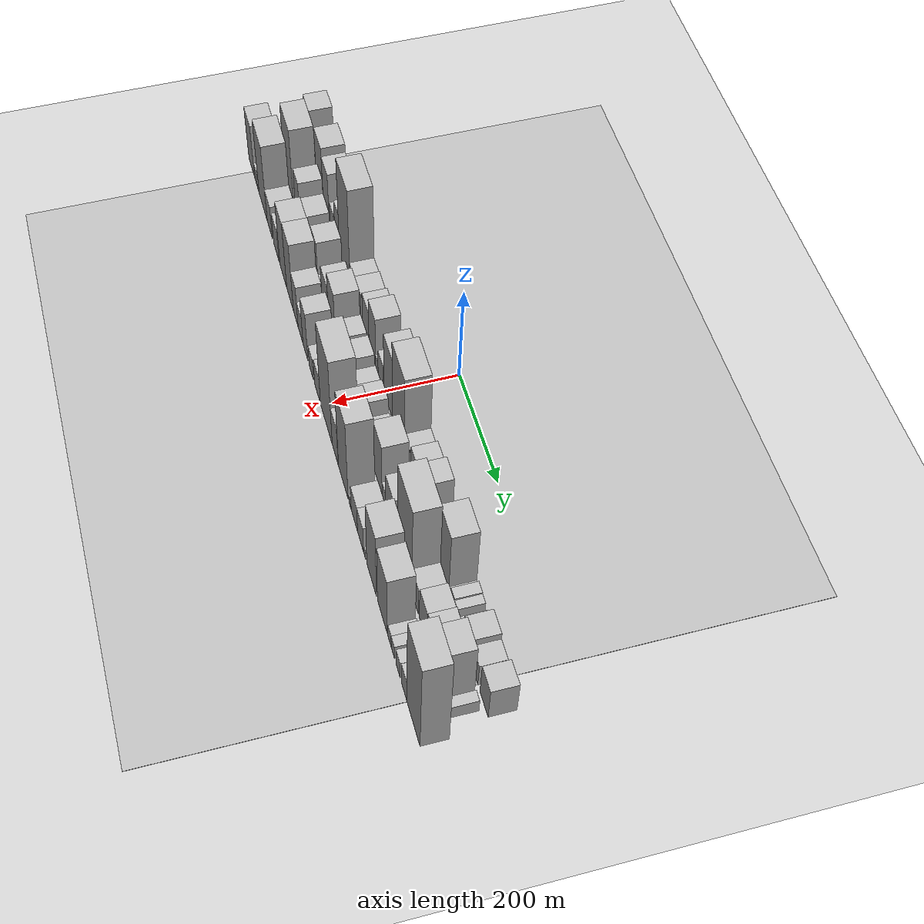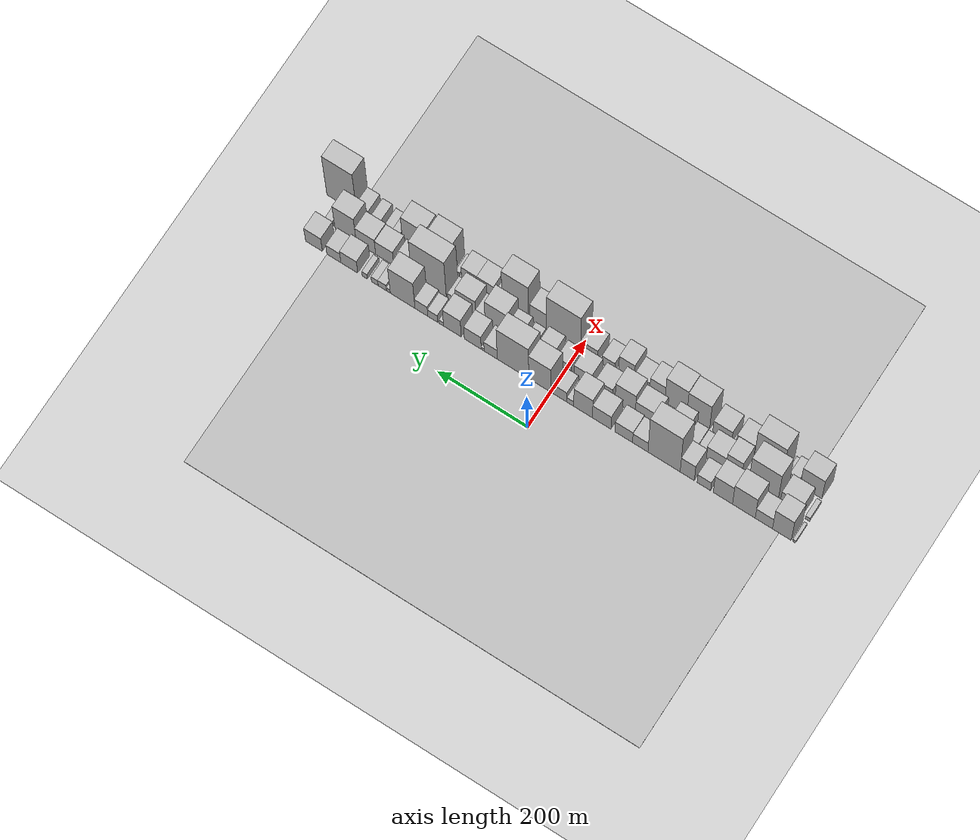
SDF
<?xml version="1.0" encoding="utf-8"?>

<sdf version="1.6">

   <world name="default">

      <gui fullscreen="0">

         <camera name="user_camera">

            <pose>-15 0 4.57585 0 0 0</pose>

            <view_controller>orbit</view_controller>

         </camera>

      </gui>

      <scene>

         <sky>

           <clouds>

             <speed>12</speed>

           </clouds>

         </sky>

         <ambient>0.4 0.4 0.4 1</ambient>

         <background>0.7 0.7 0.7 1</background>

         <shadows>1</shadows>

      </scene>

      <gravity>0 0 -9.8066</gravity>

      <magnetic_field>6e-06 2.3e-05 -4.2e-05</magnetic_field>

      <physics default="0" name="default_physics" type="ode">

         <ode>

            <solver>

               <type>quick</type>

               <iters>10</iters>

               <sor>1.0</sor>

               <use_dynamic_moi_rescaling>0</use_dynamic_moi_rescaling>

            </solver>

            <constraints>

               <cfm>0</cfm>

               <erp>0.2</erp>

               <contact_max_correcting_vel>100</contact_max_correcting_vel>

               <contact_surface_layer>0.001</contact_surface_layer>

            </constraints>

         </ode>

         <max_step_size>0.004</max_step_size>

         <real_time_factor>1</real_time_factor>

         <real_time_update_rate>250</real_time_update_rate>

      </physics>

      <light name="sun" type="directional">

         <cast_shadows>1</cast_shadows>

         <pose>0 0 10 0 0 0</pose>

         <diffuse>0.8 0.8 0.8 1</diffuse>

         <specular>0.2 0.2 0.2 1</specular>

         <attenuation>

            <range>1000</range>

            <constant>0.9</constant>

            <linear>0.01</linear>

            <quadratic>0.001</quadratic>

         </attenuation>

         <direction>-0.5 0.1 -0.9</direction>

      </light>

      <include>

         <name>ground_plane_1</name>

         <uri>model://HANNAS_ground_plane</uri>

         <pose>0 0 0  0 0 0</pose>

      </include>

      <include>

         <name>ground_plane_2</name>

         <uri>model://HANNAS_ground_plane</uri>

         <pose>100 0 0  0 0 0</pose>

      </include>

      <model name="building_1">

         <static>1</static>

         <pose frame="">100.0000 -532.6569 0 0.000000 0.000000 0.000000</pose>

         <link name="link">

            <pose frame="">0 0 7.50 0 0 0</pose>

            <collision name="collision">

               <geometry>

                  <box>

                     <size>40.0000 6.6862 15.0000</size>

                  </box>

               </geometry>

               <max_contacts>10</max_contacts>

               <surface>

                  <contact>

                     <ode/>

                  </contact>

                  <bounce/>

                  <friction>

                     <torsional>

                        <ode/>

                     </torsional>

                     <ode/>

                  </friction>

               </surface>

            </collision>

            <visual name="visual">

               <cast_shadows>0</cast_shadows>

               <geometry>

                  <box>

                     <size>40.0000 6.6862 15.0000</size>

                  </box>

               </geometry>

               <material>

                  <script>

                     <uri>model://HANNAS_wall/materials/scripts</uri>

                     <uri>model://HANNAS_wall/materials/textures</uri>

                     <name>vrc/HANNAS_wall</name>

                  </script>

               </material>

            </visual>

            <self_collide>0</self_collide>

            <enable_wind>0</enable_wind>

            <kinematic>0</kinematic>

         </link>

      </model>

      <model name="building_2">

         <static>1</static>

         <pose frame="">100.0000 -505.9349 0 0.000000 0.000000 0.000000</pose>

         <link name="link">

            <pose frame="">0 0 64.50 0 0 0</pose>

            <collision name="collision">

               <geometry>

                  <box>

                     <size>40.0000 40.7578 129.0000</size>

                  </box>

               </geometry>

               <max_contacts>10</max_contacts>

               <surface>

                  <contact>

                     <ode/>

                  </contact>

                  <bounce/>

                  <friction>

                     <torsional>

                        <ode/>

                     </torsional>

                     <ode/>

                  </friction>

               </surface>

            </collision>

            <visual name="visual">

               <cast_shadows>0</cast_shadows>

               <geometry>

                  <box>

                     <size>40.0000 40.7578 129.0000</size>

                  </box>

               </geometry>

               <material>

                  <script>

                     <uri>model://HANNAS_wall/materials/scripts</uri>

                     <uri>model://HANNAS_wall/materials/textures</uri>

                     <name>vrc/HANNAS_wall</name>

                  </script>

               </material>

            </visual>

            <self_collide>0</self_collide>

            <enable_wind>0</enable_wind>

            <kinematic>0</kinematic>

         </link>

      </model>

      <model name="building_3">

         <static>1</static>

         <pose frame="">100.0000 -466.7284 0 0.000000 0.000000 0.000000</pose>

         <link name="link">

            <pose frame="">0 0 33.00 0 0 0</pose>

            <collision name="collision">

               <geometry>

                  <box>

                     <size>40.0000 37.6552 66.0000</size>

                  </box>

               </geometry>

               <max_contacts>10</max_contacts>

               <surface>

                  <contact>

                     <ode/>

                  </contact>

                  <bounce/>

                  <friction>

                     <torsional>

                        <ode/>

                     </torsional>

                     <ode/>

                  </friction>

               </surface>

            </collision>

            <visual name="visual">

               <cast_shadows>0</cast_shadows>

               <geometry>

                  <box>

                     <size>40.0000 37.6552 66.0000</size>

                  </box>

               </geometry>

               <material>

                  <script>

                     <uri>model://HANNAS_wall/materials/scripts</uri>

                     <uri>model://HANNAS_wall/materials/textures</uri>

                     <name>vrc/HANNAS_wall</name>

                  </script>

               </material>

            </visual>

            <self_collide>0</self_collide>

            <enable_wind>0</enable_wind>

            <kinematic>0</kinematic>

         </link>

      </model>

      <model name="building_4">

         <static>1</static>

         <pose frame="">100.0000 -423.2139 0 0.000000 0.000000 0.000000</pose>

         <link name="link">

            <pose frame="">0 0 64.50 0 0 0</pose>

            <collision name="collision">

               <geometry>

                  <box>

                     <size>40.0000 49.3737 129.0000</size>

                  </box>

               </geometry>

               <max_contacts>10</max_contacts>

               <surface>

                  <contact>

                     <ode/>

                  </contact>

                  <bounce/>

                  <friction>

                     <torsional>

                        <ode/>

                     </torsional>

                     <ode/>

                  </friction>

               </surface>

            </collision>

            <visual name="visual">

               <cast_shadows>0</cast_shadows>

               <geometry>

                  <box>

                     <size>40.0000 49.3737 129.0000</size>

                  </box>

               </geometry>

               <material>

                  <script>

                     <uri>model://HANNAS_wall/materials/scripts</uri>

                     <uri>model://HANNAS_wall/materials/textures</uri>

                     <name>vrc/HANNAS_wall</name>

                  </script>

               </material>

            </visual>

            <self_collide>0</self_collide>

            <enable_wind>0</enable_wind>

            <kinematic>0</kinematic>

         </link>

      </model>

      <model name="building_5">

         <static>1</static>

         <pose frame="">100.0000 -377.5624 0 0.000000 0.000000 0.000000</pose>

         <link name="link">

            <pose frame="">0 0 55.50 0 0 0</pose>

            <collision name="collision">

               <geometry>

                  <box>

                     <size>40.0000 41.9293 111.0000</size>

                  </box>

               </geometry>

               <max_contacts>10</max_contacts>

               <surface>

                  <contact>

                     <ode/>

                  </contact>

                  <bounce/>

                  <friction>

                     <torsional>

                        <ode/>

                     </torsional>

                     <ode/>

                  </friction>

               </surface>

            </collision>

            <visual name="visual">

               <cast_shadows>0</cast_shadows>

               <geometry>

                  <box>

                     <size>40.0000 41.9293 111.0000</size>

                  </box>

               </geometry>

               <material>

                  <script>

                     <uri>model://HANNAS_wall/materials/scripts</uri>

                     <uri>model://HANNAS_wall/materials/textures</uri>

                     <name>vrc/HANNAS_wall</name>

                  </script>

               </material>

            </visual>

            <self_collide>0</self_collide>

            <enable_wind>0</enable_wind>

            <kinematic>0</kinematic>

         </link>

      </model>

      <model name="building_6">

         <static>1</static>

         <pose frame="">100.0000 -335.8281 0 0.000000 0.000000 0.000000</pose>

         <link name="link">

            <pose frame="">0 0 27.00 0 0 0</pose>

            <collision name="collision">

               <geometry>

                  <box>

                     <size>40.0000 29.5394 54.0000</size>

                  </box>

               </geometry>

               <max_contacts>10</max_contacts>

               <surface>

                  <contact>

                     <ode/>

                  </contact>

                  <bounce/>

                  <friction>

                     <torsional>

                        <ode/>

                     </torsional>

                     <ode/>

                  </friction>

               </surface>

            </collision>

            <visual name="visual">

               <cast_shadows>0</cast_shadows>

               <geometry>

                  <box>

                     <size>40.0000 29.5394 54.0000</size>

                  </box>

               </geometry>

               <material>

                  <script>

                     <uri>model://HANNAS_wall/materials/scripts</uri>

                     <uri>model://HANNAS_wall/materials/textures</uri>

                     <name>vrc/HANNAS_wall</name>

                  </script>

               </material>

            </visual>

            <self_collide>0</self_collide>

            <enable_wind>0</enable_wind>

            <kinematic>0</kinematic>

         </link>

      </model>

      <model name="building_7">

         <static>1</static>

         <pose frame="">100.0000 -299.5484 0 0.000000 0.000000 0.000000</pose>

         <link name="link">

            <pose frame="">0 0 48.00 0 0 0</pose>

            <collision name="collision">

               <geometry>

                  <box>

                     <size>40.0000 31.0200 96.0000</size>

                  </box>

               </geometry>

               <max_contacts>10</max_contacts>

               <surface>

                  <contact>

                     <ode/>

                  </contact>

                  <bounce/>

                  <friction>

                     <torsional>

                        <ode/>

                     </torsional>

                     <ode/>

                  </friction>

               </surface>

            </collision>

            <visual name="visual">

               <cast_shadows>0</cast_shadows>

               <geometry>

                  <box>

                     <size>40.0000 31.0200 96.0000</size>

                  </box>

               </geometry>

               <material>

                  <script>

                     <uri>model://HANNAS_wall/materials/scripts</uri>

                     <uri>model://HANNAS_wall/materials/textures</uri>

                     <name>vrc/HANNAS_wall</name>

                  </script>

               </material>

            </visual>

            <self_collide>0</self_collide>

            <enable_wind>0</enable_wind>

            <kinematic>0</kinematic>

         </link>

      </model>

      <model name="building_8">

         <static>1</static>

         <pose frame="">100.0000 -248.7638 0 0.000000 0.000000 0.000000</pose>

         <link name="link">

            <pose frame="">0 0 111.00 0 0 0</pose>

            <collision name="collision">

               <geometry>

                  <box>

                     <size>40.0000 70.5492 222.0000</size>

                  </box>

               </geometry>

               <max_contacts>10</max_contacts>

               <surface>

                  <contact>

                     <ode/>

                  </contact>

                  <bounce/>

                  <friction>

                     <torsional>

                        <ode/>

                     </torsional>

                     <ode/>

                  </friction>

               </surface>

            </collision>

            <visual name="visual">

               <cast_shadows>0</cast_shadows>

               <geometry>

                  <box>

                     <size>40.0000 70.5492 222.0000</size>

                  </box>

               </geometry>

               <material>

                  <script>

                     <uri>model://HANNAS_wall/materials/scripts</uri>

                     <uri>model://HANNAS_wall/materials/textures</uri>

                     <name>vrc/HANNAS_wall</name>

                  </script>

               </material>

            </visual>

            <self_collide>0</self_collide>

            <enable_wind>0</enable_wind>

            <kinematic>0</kinematic>

         </link>

      </model>

      <model name="building_9">

         <static>1</static>

         <pose frame="">100.0000 -196.5476 0 0.000000 0.000000 0.000000</pose>

         <link name="link">

            <pose frame="">0 0 30.00 0 0 0</pose>

            <collision name="collision">

               <geometry>

                  <box>

                     <size>40.0000 33.8831 60.0000</size>

                  </box>

               </geometry>

               <max_contacts>10</max_contacts>

               <surface>

                  <contact>

                     <ode/>

                  </contact>

                  <bounce/>

                  <friction>

                     <torsional>

                        <ode/>

                     </torsional>

                     <ode/>

                  </friction>

               </surface>

            </collision>

            <visual name="visual">

               <cast_shadows>0</cast_shadows>

               <geometry>

                  <box>

                     <size>40.0000 33.8831 60.0000</size>

                  </box>

               </geometry>

               <material>

                  <script>

                     <uri>model://HANNAS_wall/materials/scripts</uri>

                     <uri>model://HANNAS_wall/materials/textures</uri>

                     <name>vrc/HANNAS_wall</name>

                  </script>

               </material>

            </visual>

            <self_collide>0</self_collide>

            <enable_wind>0</enable_wind>

            <kinematic>0</kinematic>

         </link>

      </model>

      <model name="building_10">

         <static>1</static>

         <pose frame="">100.0000 -160.3674 0 0.000000 0.000000 0.000000</pose>

         <link name="link">

            <pose frame="">0 0 33.00 0 0 0</pose>

            <collision name="collision">

               <geometry>

                  <box>

                     <size>40.0000 38.4773 66.0000</size>

                  </box>

               </geometry>

               <max_contacts>10</max_contacts>

               <surface>

                  <contact>

                     <ode/>

                  </contact>

                  <bounce/>

                  <friction>

                     <torsional>

                        <ode/>

                     </torsional>

                     <ode/>

                  </friction>

               </surface>

            </collision>

            <visual name="visual">

               <cast_shadows>0</cast_shadows>

               <geometry>

                  <box>

                     <size>40.0000 38.4773 66.0000</size>

                  </box>

               </geometry>

               <material>

                  <script>

                     <uri>model://HANNAS_wall/materials/scripts</uri>

                     <uri>model://HANNAS_wall/materials/textures</uri>

                     <name>vrc/HANNAS_wall</name>

                  </script>

               </material>

            </visual>

            <self_collide>0</self_collide>

            <enable_wind>0</enable_wind>

            <kinematic>0</kinematic>

         </link>

      </model>

      <model name="building_11">

         <static>1</static>

         <pose frame="">100.0000 -111.7872 0 0.000000 0.000000 0.000000</pose>

         <link name="link">

            <pose frame="">0 0 40.50 0 0 0</pose>

            <collision name="collision">

               <geometry>

                  <box>

                     <size>40.0000 40.6831 81.0000</size>

                  </box>

               </geometry>

               <max_contacts>10</max_contacts>

               <surface>

                  <contact>

                     <ode/>

                  </contact>

                  <bounce/>

                  <friction>

                     <torsional>

                        <ode/>

                     </torsional>

                     <ode/>

                  </friction>

               </surface>

            </collision>

            <visual name="visual">

               <cast_shadows>0</cast_shadows>

               <geometry>

                  <box>

                     <size>40.0000 40.6831 81.0000</size>

                  </box>

               </geometry>

               <material>

                  <script>

                     <uri>model://HANNAS_wall/materials/scripts</uri>

                     <uri>model://HANNAS_wall/materials/textures</uri>

                     <name>vrc/HANNAS_wall</name>

                  </script>

               </material>

            </visual>

            <self_collide>0</self_collide>

            <enable_wind>0</enable_wind>

            <kinematic>0</kinematic>

         </link>

      </model>

      <model name="building_12">

         <static>1</static>

         <pose frame="">100.0000 -70.7702 0 0.000000 0.000000 0.000000</pose>

         <link name="link">

            <pose frame="">0 0 57.00 0 0 0</pose>

            <collision name="collision">

               <geometry>

                  <box>

                     <size>40.0000 41.3510 114.0000</size>

                  </box>

               </geometry>

               <max_contacts>10</max_contacts>

               <surface>

                  <contact>

                     <ode/>

                  </contact>

                  <bounce/>

                  <friction>

                     <torsional>

                        <ode/>

                     </torsional>

                     <ode/>

                  </friction>

               </surface>

            </collision>

            <visual name="visual">

               <cast_shadows>0</cast_shadows>

               <geometry>

                  <box>

                     <size>40.0000 41.3510 114.0000</size>

                  </box>

               </geometry>

               <material>

                  <script>

                     <uri>model://HANNAS_wall/materials/scripts</uri>

                     <uri>model://HANNAS_wall/materials/textures</uri>

                     <name>vrc/HANNAS_wall</name>

                  </script>

               </material>

            </visual>

            <self_collide>0</self_collide>

            <enable_wind>0</enable_wind>

            <kinematic>0</kinematic>

         </link>

      </model>

      <model name="building_13">

         <static>1</static>

         <pose frame="">100.0000 -42.5535 0 0.000000 0.000000 0.000000</pose>

         <link name="link">

            <pose frame="">0 0 15.00 0 0 0</pose>

            <collision name="collision">

               <geometry>

                  <box>

                     <size>40.0000 15.0822 30.0000</size>

                  </box>

               </geometry>

               <max_contacts>10</max_contacts>

               <surface>

                  <contact>

                     <ode/>

                  </contact>

                  <bounce/>

                  <friction>

                     <torsional>

                        <ode/>

                     </torsional>

                     <ode/>

                  </friction>

               </surface>

            </collision>

            <visual name="visual">

               <cast_shadows>0</cast_shadows>

               <geometry>

                  <box>

                     <size>40.0000 15.0822 30.0000</size>

                  </box>

               </geometry>

               <material>

                  <script>

                     <uri>model://HANNAS_wall/materials/scripts</uri>

                     <uri>model://HANNAS_wall/materials/textures</uri>

                     <name>vrc/HANNAS_wall</name>

                  </script>

               </material>

            </visual>

            <self_collide>0</self_collide>

            <enable_wind>0</enable_wind>

            <kinematic>0</kinematic>

         </link>

      </model>

      <model name="building_14">

         <static>1</static>

         <pose frame="">100.0000 -19.4573 0 0.000000 0.000000 0.000000</pose>

         <link name="link">

            <pose frame="">0 0 30.00 0 0 0</pose>

            <collision name="collision">

               <geometry>

                  <box>

                     <size>40.0000 31.1103 60.0000</size>

                  </box>

               </geometry>

               <max_contacts>10</max_contacts>

               <surface>

                  <contact>

                     <ode/>

                  </contact>

                  <bounce/>

                  <friction>

                     <torsional>

                        <ode/>

                     </torsional>

                     <ode/>

                  </friction>

               </surface>

            </collision>

            <visual name="visual">

               <cast_shadows>0</cast_shadows>

               <geometry>

                  <box>

                     <size>40.0000 31.1103 60.0000</size>

                  </box>

               </geometry>

               <material>

                  <script>

                     <uri>model://HANNAS_wall/materials/scripts</uri>

                     <uri>model://HANNAS_wall/materials/textures</uri>

                     <name>vrc/HANNAS_wall</name>

                  </script>

               </material>

            </visual>

            <self_collide>0</self_collide>

            <enable_wind>0</enable_wind>

            <kinematic>0</kinematic>

         </link>

      </model>

      <model name="building_15">

         <static>1</static>

         <pose frame="">100.0000 24.7124 0 0.000000 0.000000 0.000000</pose>

         <link name="link">

            <pose frame="">0 0 72.00 0 0 0</pose>

            <collision name="collision">

               <geometry>

                  <box>

                     <size>40.0000 49.2291 144.0000</size>

                  </box>

               </geometry>

               <max_contacts>10</max_contacts>

               <surface>

                  <contact>

                     <ode/>

                  </contact>

                  <bounce/>

                  <friction>

                     <torsional>

                        <ode/>

                     </torsional>

                     <ode/>

                  </friction>

               </surface>

            </collision>

            <visual name="visual">

               <cast_shadows>0</cast_shadows>

               <geometry>

                  <box>

                     <size>40.0000 49.2291 144.0000</size>

                  </box>

               </geometry>

               <material>

                  <script>

                     <uri>model://HANNAS_wall/materials/scripts</uri>

                     <uri>model://HANNAS_wall/materials/textures</uri>

                     <name>vrc/HANNAS_wall</name>

                  </script>

               </material>

            </visual>

            <self_collide>0</self_collide>

            <enable_wind>0</enable_wind>

            <kinematic>0</kinematic>

         </link>

      </model>

      <model name="building_16">

         <static>1</static>

         <pose frame="">100.0000 84.3406 0 0.000000 0.000000 0.000000</pose>

         <link name="link">

            <pose frame="">0 0 93.00 0 0 0</pose>

            <collision name="collision">

               <geometry>

                  <box>

                     <size>40.0000 70.0272 186.0000</size>

                  </box>

               </geometry>

               <max_contacts>10</max_contacts>

               <surface>

                  <contact>

                     <ode/>

                  </contact>

                  <bounce/>

                  <friction>

                     <torsional>

                        <ode/>

                     </torsional>

                     <ode/>

                  </friction>

               </surface>

            </collision>

            <visual name="visual">

               <cast_shadows>0</cast_shadows>

               <geometry>

                  <box>

                     <size>40.0000 70.0272 186.0000</size>

                  </box>

               </geometry>

               <material>

                  <script>

                     <uri>model://HANNAS_wall/materials/scripts</uri>

                     <uri>model://HANNAS_wall/materials/textures</uri>

                     <name>vrc/HANNAS_wall</name>

                  </script>

               </material>

            </visual>

            <self_collide>0</self_collide>

            <enable_wind>0</enable_wind>

            <kinematic>0</kinematic>

         </link>

      </model>

      <model name="building_17">

         <static>1</static>

         <pose frame="">100.0000 133.8959 0 0.000000 0.000000 0.000000</pose>

         <link name="link">

            <pose frame="">0 0 28.50 0 0 0</pose>

            <collision name="collision">

               <geometry>

                  <box>

                     <size>40.0000 29.0835 57.0000</size>

                  </box>

               </geometry>

               <max_contacts>10</max_contacts>

               <surface>

                  <contact>

                     <ode/>

                  </contact>

                  <bounce/>

                  <friction>

                     <torsional>

                        <ode/>

                     </torsional>

                     <ode/>

                  </friction>

               </surface>

            </collision>

            <visual name="visual">

               <cast_shadows>0</cast_shadows>

               <geometry>

                  <box>

                     <size>40.0000 29.0835 57.0000</size>

                  </box>

               </geometry>

               <material>

                  <script>

                     <uri>model://HANNAS_wall/materials/scripts</uri>

                     <uri>model://HANNAS_wall/materials/textures</uri>

                     <name>vrc/HANNAS_wall</name>

                  </script>

               </material>

            </visual>

            <self_collide>0</self_collide>

            <enable_wind>0</enable_wind>

            <kinematic>0</kinematic>

         </link>

      </model>

      <model name="building_18">

         <static>1</static>

         <pose frame="">100.0000 151.7411 0 0.000000 0.000000 0.000000</pose>

         <link name="link">

            <pose frame="">0 0 7.50 0 0 0</pose>

            <collision name="collision">

               <geometry>

                  <box>

                     <size>40.0000 6.6067 15.0000</size>

                  </box>

               </geometry>

               <max_contacts>10</max_contacts>

               <surface>

                  <contact>

                     <ode/>

                  </contact>

                  <bounce/>

                  <friction>

                     <torsional>

                        <ode/>

                     </torsional>

                     <ode/>

                  </friction>

               </surface>

            </collision>

            <visual name="visual">

               <cast_shadows>0</cast_shadows>

               <geometry>

                  <box>

                     <size>40.0000 6.6067 15.0000</size>

                  </box>

               </geometry>

               <material>

                  <script>

                     <uri>model://HANNAS_wall/materials/scripts</uri>

                     <uri>model://HANNAS_wall/materials/textures</uri>

                     <name>vrc/HANNAS_wall</name>

                  </script>

               </material>

            </visual>

            <self_collide>0</self_collide>

            <enable_wind>0</enable_wind>

            <kinematic>0</kinematic>

         </link>

      </model>

      <model name="building_19">

         <static>1</static>

         <pose frame="">100.0000 173.7985 0 0.000000 0.000000 0.000000</pose>

         <link name="link">

            <pose frame="">0 0 37.50 0 0 0</pose>

            <collision name="collision">

               <geometry>

                  <box>

                     <size>40.0000 37.5081 75.0000</size>

                  </box>

               </geometry>

               <max_contacts>10</max_contacts>

               <surface>

                  <contact>

                     <ode/>

                  </contact>

                  <bounce/>

                  <friction>

                     <torsional>

                        <ode/>

                     </torsional>

                     <ode/>

                  </friction>

               </surface>

            </collision>

            <visual name="visual">

               <cast_shadows>0</cast_shadows>

               <geometry>

                  <box>

                     <size>40.0000 37.5081 75.0000</size>

                  </box>

               </geometry>

               <material>

                  <script>

                     <uri>model://HANNAS_wall/materials/scripts</uri>

                     <uri>model://HANNAS_wall/materials/textures</uri>

                     <name>vrc/HANNAS_wall</name>

                  </script>

               </material>

            </visual>

            <self_collide>0</self_collide>

            <enable_wind>0</enable_wind>

            <kinematic>0</kinematic>

         </link>

      </model>

      <model name="building_20">

         <static>1</static>

         <pose frame="">100.0000 219.1859 0 0.000000 0.000000 0.000000</pose>

         <link name="link">

            <pose frame="">0 0 49.50 0 0 0</pose>

            <collision name="collision">

               <geometry>

                  <box>

                     <size>40.0000 39.2666 99.0000</size>

                  </box>

               </geometry>

               <max_contacts>10</max_contacts>

               <surface>

                  <contact>

                     <ode/>

                  </contact>

                  <bounce/>

                  <friction>

                     <torsional>

                        <ode/>

                     </torsional>

                     <ode/>

                  </friction>

               </surface>

            </collision>

            <visual name="visual">

               <cast_shadows>0</cast_shadows>

               <geometry>

                  <box>

                     <size>40.0000 39.2666 99.0000</size>

                  </box>

               </geometry>

               <material>

                  <script>

                     <uri>model://HANNAS_wall/materials/scripts</uri>

                     <uri>model://HANNAS_wall/materials/textures</uri>

                     <name>vrc/HANNAS_wall</name>

                  </script>

               </material>

            </visual>

            <self_collide>0</self_collide>

            <enable_wind>0</enable_wind>

            <kinematic>0</kinematic>

         </link>

      </model>

      <model name="building_21">

         <static>1</static>

         <pose frame="">100.0000 243.8342 0 0.000000 0.000000 0.000000</pose>

         <link name="link">

            <pose frame="">0 0 10.50 0 0 0</pose>

            <collision name="collision">

               <geometry>

                  <box>

                     <size>40.0000 10.0301 21.0000</size>

                  </box>

               </geometry>

               <max_contacts>10</max_contacts>

               <surface>

                  <contact>

                     <ode/>

                  </contact>

                  <bounce/>

                  <friction>

                     <torsional>

                        <ode/>

                     </torsional>

                     <ode/>

                  </friction>

               </surface>

            </collision>

            <visual name="visual">

               <cast_shadows>0</cast_shadows>

               <geometry>

                  <box>

                     <size>40.0000 10.0301 21.0000</size>

                  </box>

               </geometry>

               <material>

                  <script>

                     <uri>model://HANNAS_wall/materials/scripts</uri>

                     <uri>model://HANNAS_wall/materials/textures</uri>

                     <name>vrc/HANNAS_wall</name>

                  </script>

               </material>

            </visual>

            <self_collide>0</self_collide>

            <enable_wind>0</enable_wind>

            <kinematic>0</kinematic>

         </link>

      </model>

      <model name="building_22">

         <static>1</static>

         <pose frame="">100.0000 262.9086 0 0.000000 0.000000 0.000000</pose>

         <link name="link">

            <pose frame="">0 0 21.00 0 0 0</pose>

            <collision name="collision">

               <geometry>

                  <box>

                     <size>40.0000 22.1185 42.0000</size>

                  </box>

               </geometry>

               <max_contacts>10</max_contacts>

               <surface>

                  <contact>

                     <ode/>

                  </contact>

                  <bounce/>

                  <friction>

                     <torsional>

                        <ode/>

                     </torsional>

                     <ode/>

                  </friction>

               </surface>

            </collision>

            <visual name="visual">

               <cast_shadows>0</cast_shadows>

               <geometry>

                  <box>

                     <size>40.0000 22.1185 42.0000</size>

                  </box>

               </geometry>

               <material>

                  <script>

                     <uri>model://HANNAS_wall/materials/scripts</uri>

                     <uri>model://HANNAS_wall/materials/textures</uri>

                     <name>vrc/HANNAS_wall</name>

                  </script>

               </material>

            </visual>

            <self_collide>0</self_collide>

            <enable_wind>0</enable_wind>

            <kinematic>0</kinematic>

         </link>

      </model>

      <model name="building_23">

         <static>1</static>

         <pose frame="">100.0000 288.2945 0 0.000000 0.000000 0.000000</pose>

         <link name="link">

            <pose frame="">0 0 28.50 0 0 0</pose>

            <collision name="collision">

               <geometry>

                  <box>

                     <size>40.0000 28.6533 57.0000</size>

                  </box>

               </geometry>

               <max_contacts>10</max_contacts>

               <surface>

                  <contact>

                     <ode/>

                  </contact>

                  <bounce/>

                  <friction>

                     <torsional>

                        <ode/>

                     </torsional>

                     <ode/>

                  </friction>

               </surface>

            </collision>

            <visual name="visual">

               <cast_shadows>0</cast_shadows>

               <geometry>

                  <box>

                     <size>40.0000 28.6533 57.0000</size>

                  </box>

               </geometry>

               <material>

                  <script>

                     <uri>model://HANNAS_wall/materials/scripts</uri>

                     <uri>model://HANNAS_wall/materials/textures</uri>

                     <name>vrc/HANNAS_wall</name>

                  </script>

               </material>

            </visual>

            <self_collide>0</self_collide>

            <enable_wind>0</enable_wind>

            <kinematic>0</kinematic>

         </link>

      </model>

      <model name="building_24">

         <static>1</static>

         <pose frame="">100.0000 330.2914 0 0.000000 0.000000 0.000000</pose>

         <link name="link">

            <pose frame="">0 0 75.00 0 0 0</pose>

            <collision name="collision">

               <geometry>

                  <box>

                     <size>40.0000 55.3407 150.0000</size>

                  </box>

               </geometry>

               <max_contacts>10</max_contacts>

               <surface>

                  <contact>

                     <ode/>

                  </contact>

                  <bounce/>

                  <friction>

                     <torsional>

                        <ode/>

                     </torsional>

                     <ode/>

                  </friction>

               </surface>

            </collision>

            <visual name="visual">

               <cast_shadows>0</cast_shadows>

               <geometry>

                  <box>

                     <size>40.0000 55.3407 150.0000</size>

                  </box>

               </geometry>

               <material>

                  <script>

                     <uri>model://HANNAS_wall/materials/scripts</uri>

                     <uri>model://HANNAS_wall/materials/textures</uri>

                     <name>vrc/HANNAS_wall</name>

                  </script>

               </material>

            </visual>

            <self_collide>0</self_collide>

            <enable_wind>0</enable_wind>

            <kinematic>0</kinematic>

         </link>

      </model>

      <model name="building_25">

         <static>1</static>

         <pose frame="">100.0000 362.2287 0 0.000000 0.000000 0.000000</pose>

         <link name="link">

            <pose frame="">0 0 10.50 0 0 0</pose>

            <collision name="collision">

               <geometry>

                  <box>

                     <size>40.0000 8.5337 21.0000</size>

                  </box>

               </geometry>

               <max_contacts>10</max_contacts>

               <surface>

                  <contact>

                     <ode/>

                  </contact>

                  <bounce/>

                  <friction>

                     <torsional>

                        <ode/>

                     </torsional>

                     <ode/>

                  </friction>

               </surface>

            </collision>

            <visual name="visual">

               <cast_shadows>0</cast_shadows>

               <geometry>

                  <box>

                     <size>40.0000 8.5337 21.0000</size>

                  </box>

               </geometry>

               <material>

                  <script>

                     <uri>model://HANNAS_wall/materials/scripts</uri>

                     <uri>model://HANNAS_wall/materials/textures</uri>

                     <name>vrc/HANNAS_wall</name>

                  </script>

               </material>

            </visual>

            <self_collide>0</self_collide>

            <enable_wind>0</enable_wind>

            <kinematic>0</kinematic>

         </link>

      </model>

      <model name="building_26">

         <static>1</static>

         <pose frame="">100.0000 375.7533 0 0.000000 0.000000 0.000000</pose>

         <link name="link">

            <pose frame="">0 0 16.50 0 0 0</pose>

            <collision name="collision">

               <geometry>

                  <box>

                     <size>40.0000 18.5155 33.0000</size>

                  </box>

               </geometry>

               <max_contacts>10</max_contacts>

               <surface>

                  <contact>

                     <ode/>

                  </contact>

                  <bounce/>

                  <friction>

                     <torsional>

                        <ode/>

                     </torsional>

                     <ode/>

                  </friction>

               </surface>

            </collision>

            <visual name="visual">

               <cast_shadows>0</cast_shadows>

               <geometry>

                  <box>

                     <size>40.0000 18.5155 33.0000</size>

                  </box>

               </geometry>

               <material>

                  <script>

                     <uri>model://HANNAS_wall/materials/scripts</uri>

                     <uri>model://HANNAS_wall/materials/textures</uri>

                     <name>vrc/HANNAS_wall</name>

                  </script>

               </material>

            </visual>

            <self_collide>0</self_collide>

            <enable_wind>0</enable_wind>

            <kinematic>0</kinematic>

         </link>

      </model>

      <model name="building_27">

         <static>1</static>

         <pose frame="">100.0000 392.5887 0 0.000000 0.000000 0.000000</pose>

         <link name="link">

            <pose frame="">0 0 15.00 0 0 0</pose>

            <collision name="collision">

               <geometry>

                  <box>

                     <size>40.0000 15.1554 30.0000</size>

                  </box>

               </geometry>

               <max_contacts>10</max_contacts>

               <surface>

                  <contact>

                     <ode/>

                  </contact>

                  <bounce/>

                  <friction>

                     <torsional>

                        <ode/>

                     </torsional>

                     <ode/>

                  </friction>

               </surface>

            </collision>

            <visual name="visual">

               <cast_shadows>0</cast_shadows>

               <geometry>

                  <box>

                     <size>40.0000 15.1554 30.0000</size>

                  </box>

               </geometry>

               <material>

                  <script>

                     <uri>model://HANNAS_wall/materials/scripts</uri>

                     <uri>model://HANNAS_wall/materials/textures</uri>

                     <name>vrc/HANNAS_wall</name>

                  </script>

               </material>

            </visual>

            <self_collide>0</self_collide>

            <enable_wind>0</enable_wind>

            <kinematic>0</kinematic>

         </link>

      </model>

      <model name="building_28">

         <static>1</static>

         <pose frame="">100.0000 415.0585 0 0.000000 0.000000 0.000000</pose>

         <link name="link">

            <pose frame="">0 0 13.50 0 0 0</pose>

            <collision name="collision">

               <geometry>

                  <box>

                     <size>40.0000 11.7842 27.0000</size>

                  </box>

               </geometry>

               <max_contacts>10</max_contacts>

               <surface>

                  <contact>

                     <ode/>

                  </contact>

                  <bounce/>

                  <friction>

                     <torsional>

                        <ode/>

                     </torsional>

                     <ode/>

                  </friction>

               </surface>

            </collision>

            <visual name="visual">

               <cast_shadows>0</cast_shadows>

               <geometry>

                  <box>

                     <size>40.0000 11.7842 27.0000</size>

                  </box>

               </geometry>

               <material>

                  <script>

                     <uri>model://HANNAS_wall/materials/scripts</uri>

                     <uri>model://HANNAS_wall/materials/textures</uri>

                     <name>vrc/HANNAS_wall</name>

                  </script>

               </material>

            </visual>

            <self_collide>0</self_collide>

            <enable_wind>0</enable_wind>

            <kinematic>0</kinematic>

         </link>

      </model>

      <model name="building_29">

         <static>1</static>

         <pose frame="">100.0000 449.8755 0 0.000000 0.000000 0.000000</pose>

         <link name="link">

            <pose frame="">0 0 34.50 0 0 0</pose>

            <collision name="collision">

               <geometry>

                  <box>

                     <size>40.0000 37.8498 69.0000</size>

                  </box>

               </geometry>

               <max_contacts>10</max_contacts>

               <surface>

                  <contact>

                     <ode/>

                  </contact>

                  <bounce/>

                  <friction>

                     <torsional>

                        <ode/>

                     </torsional>

                     <ode/>

                  </friction>

               </surface>

            </collision>

            <visual name="visual">

               <cast_shadows>0</cast_shadows>

               <geometry>

                  <box>

                     <size>40.0000 37.8498 69.0000</size>

                  </box>

               </geometry>

               <material>

                  <script>

                     <uri>model://HANNAS_wall/materials/scripts</uri>

                     <uri>model://HANNAS_wall/materials/textures</uri>

                     <name>vrc/HANNAS_wall</name>

                  </script>

               </material>

            </visual>

            <self_collide>0</self_collide>

            <enable_wind>0</enable_wind>

            <kinematic>0</kinematic>

         </link>

      </model>

      <model name="building_30">

         <static>1</static>

         <pose frame="">100.0000 484.6062 0 0.000000 0.000000 0.000000</pose>

         <link name="link">

            <pose frame="">0 0 27.00 0 0 0</pose>

            <collision name="collision">

               <geometry>

                  <box>

                     <size>40.0000 31.6116 54.0000</size>

                  </box>

               </geometry>

               <max_contacts>10</max_contacts>

               <surface>

                  <contact>

                     <ode/>

                  </contact>

                  <bounce/>

                  <friction>

                     <torsional>

                        <ode/>

                     </torsional>

                     <ode/>

                  </friction>

               </surface>

            </collision>

            <visual name="visual">

               <cast_shadows>0</cast_shadows>

               <geometry>

                  <box>

                     <size>40.0000 31.6116 54.0000</size>

                  </box>

               </geometry>

               <material>

                  <script>

                     <uri>model://HANNAS_wall/materials/scripts</uri>

                     <uri>model://HANNAS_wall/materials/textures</uri>

                     <name>vrc/HANNAS_wall</name>

                  </script>

               </material>

            </visual>

            <self_collide>0</self_collide>

            <enable_wind>0</enable_wind>

            <kinematic>0</kinematic>

         </link>

      </model>

      <model name="building_31">

         <static>1</static>

         <pose frame="">100.0000 529.4154 0 0.000000 0.000000 0.000000</pose>

         <link name="link">

            <pose frame="">0 0 37.50 0 0 0</pose>

            <collision name="collision">

               <geometry>

                  <box>

                     <size>40.0000 38.0069 75.0000</size>

                  </box>

               </geometry>

               <max_contacts>10</max_contacts>

               <surface>

                  <contact>

                     <ode/>

                  </contact>

                  <bounce/>

                  <friction>

                     <torsional>

                        <ode/>

                     </torsional>

                     <ode/>

                  </friction>

               </surface>

            </collision>

            <visual name="visual">

               <cast_shadows>0</cast_shadows>

               <geometry>

                  <box>

                     <size>40.0000 38.0069 75.0000</size>

                  </box>

               </geometry>

               <material>

                  <script>

                     <uri>model://HANNAS_wall/materials/scripts</uri>

                     <uri>model://HANNAS_wall/materials/textures</uri>

                     <name>vrc/HANNAS_wall</name>

                  </script>

               </material>

            </visual>

            <self_collide>0</self_collide>

            <enable_wind>0</enable_wind>

            <kinematic>0</kinematic>

         </link>

      </model>

      <model name="building_32">

         <static>1</static>

         <pose frame="">149.0000 -531.0067 0 0.000000 0.000000 0.000000</pose>

         <link name="link">

            <pose frame="">0 0 10.50 0 0 0</pose>

            <collision name="collision">

               <geometry>

                  <box>

                     <size>40.0000 9.9865 21.0000</size>

                  </box>

               </geometry>

               <max_contacts>10</max_contacts>

               <surface>

                  <contact>

                     <ode/>

                  </contact>

                  <bounce/>

                  <friction>

                     <torsional>

                        <ode/>

                     </torsional>

                     <ode/>

                  </friction>

               </surface>

            </collision>

            <visual name="visual">

               <cast_shadows>0</cast_shadows>

               <geometry>

                  <box>

                     <size>40.0000 9.9865 21.0000</size>

                  </box>

               </geometry>

               <material>

                  <script>

                     <uri>model://HANNAS_wall/materials/scripts</uri>

                     <uri>model://HANNAS_wall/materials/textures</uri>

                     <name>vrc/HANNAS_wall</name>

                  </script>

               </material>

            </visual>

            <self_collide>0</self_collide>

            <enable_wind>0</enable_wind>

            <kinematic>0</kinematic>

         </link>

      </model>

      <model name="building_33">

         <static>1</static>

         <pose frame="">149.0000 -495.3012 0 0.000000 0.000000 0.000000</pose>

         <link name="link">

            <pose frame="">0 0 40.50 0 0 0</pose>

            <collision name="collision">

               <geometry>

                  <box>

                     <size>40.0000 47.4246 81.0000</size>

                  </box>

               </geometry>

               <max_contacts>10</max_contacts>

               <surface>

                  <contact>

                     <ode/>

                  </contact>

                  <bounce/>

                  <friction>

                     <torsional>

                        <ode/>

                     </torsional>

                     <ode/>

                  </friction>

               </surface>

            </collision>

            <visual name="visual">

               <cast_shadows>0</cast_shadows>

               <geometry>

                  <box>

                     <size>40.0000 47.4246 81.0000</size>

                  </box>

               </geometry>

               <material>

                  <script>

                     <uri>model://HANNAS_wall/materials/scripts</uri>

                     <uri>model://HANNAS_wall/materials/textures</uri>

                     <name>vrc/HANNAS_wall</name>

                  </script>

               </material>

            </visual>

            <self_collide>0</self_collide>

            <enable_wind>0</enable_wind>

            <kinematic>0</kinematic>

         </link>

      </model>

      <model name="building_34">

         <static>1</static>

         <pose frame="">149.0000 -434.6481 0 0.000000 0.000000 0.000000</pose>

         <link name="link">

            <pose frame="">0 0 88.50 0 0 0</pose>

            <collision name="collision">

               <geometry>

                  <box>

                     <size>40.0000 63.8814 177.0000</size>

                  </box>

               </geometry>

               <max_contacts>10</max_contacts>

               <surface>

                  <contact>

                     <ode/>

                  </contact>

                  <bounce/>

                  <friction>

                     <torsional>

                        <ode/>

                     </torsional>

                     <ode/>

                  </friction>

               </surface>

            </collision>

            <visual name="visual">

               <cast_shadows>0</cast_shadows>

               <geometry>

                  <box>

                     <size>40.0000 63.8814 177.0000</size>

                  </box>

               </geometry>

               <material>

                  <script>

                     <uri>model://HANNAS_wall/materials/scripts</uri>

                     <uri>model://HANNAS_wall/materials/textures</uri>

                     <name>vrc/HANNAS_wall</name>

                  </script>

               </material>

            </visual>

            <self_collide>0</self_collide>

            <enable_wind>0</enable_wind>

            <kinematic>0</kinematic>

         </link>

      </model>

      <model name="building_35">

         <static>1</static>

         <pose frame="">149.0000 -395.0903 0 0.000000 0.000000 0.000000</pose>

         <link name="link">

            <pose frame="">0 0 15.00 0 0 0</pose>

            <collision name="collision">

               <geometry>

                  <box>

                     <size>40.0000 15.2344 30.0000</size>

                  </box>

               </geometry>

               <max_contacts>10</max_contacts>

               <surface>

                  <contact>

                     <ode/>

                  </contact>

                  <bounce/>

                  <friction>

                     <torsional>

                        <ode/>

                     </torsional>

                     <ode/>

                  </friction>

               </surface>

            </collision>

            <visual name="visual">

               <cast_shadows>0</cast_shadows>

               <geometry>

                  <box>

                     <size>40.0000 15.2344 30.0000</size>

                  </box>

               </geometry>

               <material>

                  <script>

                     <uri>model://HANNAS_wall/materials/scripts</uri>

                     <uri>model://HANNAS_wall/materials/textures</uri>

                     <name>vrc/HANNAS_wall</name>

                  </script>

               </material>

            </visual>

            <self_collide>0</self_collide>

            <enable_wind>0</enable_wind>

            <kinematic>0</kinematic>

         </link>

      </model>

      <model name="building_36">

         <static>1</static>

         <pose frame="">149.0000 -370.2064 0 0.000000 0.000000 0.000000</pose>

         <link name="link">

            <pose frame="">0 0 54.00 0 0 0</pose>

            <collision name="collision">

               <geometry>

                  <box>

                     <size>40.0000 34.5334 108.0000</size>

                  </box>

               </geometry>

               <max_contacts>10</max_contacts>

               <surface>

                  <contact>

                     <ode/>

                  </contact>

                  <bounce/>

                  <friction>

                     <torsional>

                        <ode/>

                     </torsional>

                     <ode/>

                  </friction>

               </surface>

            </collision>

            <visual name="visual">

               <cast_shadows>0</cast_shadows>

               <geometry>

                  <box>

                     <size>40.0000 34.5334 108.0000</size>

                  </box>

               </geometry>

               <material>

                  <script>

                     <uri>model://HANNAS_wall/materials/scripts</uri>

                     <uri>model://HANNAS_wall/materials/textures</uri>

                     <name>vrc/HANNAS_wall</name>

                  </script>

               </material>

            </visual>

            <self_collide>0</self_collide>

            <enable_wind>0</enable_wind>

            <kinematic>0</kinematic>

         </link>

      </model>

      <model name="building_37">

         <static>1</static>

         <pose frame="">149.0000 -331.3263 0 0.000000 0.000000 0.000000</pose>

         <link name="link">

            <pose frame="">0 0 37.50 0 0 0</pose>

            <collision name="collision">

               <geometry>

                  <box>

                     <size>40.0000 43.2267 75.0000</size>

                  </box>

               </geometry>

               <max_contacts>10</max_contacts>

               <surface>

                  <contact>

                     <ode/>

                  </contact>

                  <bounce/>

                  <friction>

                     <torsional>

                        <ode/>

                     </torsional>

                     <ode/>

                  </friction>

               </surface>

            </collision>

            <visual name="visual">

               <cast_shadows>0</cast_shadows>

               <geometry>

                  <box>

                     <size>40.0000 43.2267 75.0000</size>

                  </box>

               </geometry>

               <material>

                  <script>

                     <uri>model://HANNAS_wall/materials/scripts</uri>

                     <uri>model://HANNAS_wall/materials/textures</uri>

                     <name>vrc/HANNAS_wall</name>

                  </script>

               </material>

            </visual>

            <self_collide>0</self_collide>

            <enable_wind>0</enable_wind>

            <kinematic>0</kinematic>

         </link>

      </model>

      <model name="building_38">

         <static>1</static>

         <pose frame="">149.0000 -299.9384 0 0.000000 0.000000 0.000000</pose>

         <link name="link">

            <pose frame="">0 0 16.50 0 0 0</pose>

            <collision name="collision">

               <geometry>

                  <box>

                     <size>40.0000 19.5491 33.0000</size>

                  </box>

               </geometry>

               <max_contacts>10</max_contacts>

               <surface>

                  <contact>

                     <ode/>

                  </contact>

                  <bounce/>

                  <friction>

                     <torsional>

                        <ode/>

                     </torsional>

                     <ode/>

                  </friction>

               </surface>

            </collision>

            <visual name="visual">

               <cast_shadows>0</cast_shadows>

               <geometry>

                  <box>

                     <size>40.0000 19.5491 33.0000</size>

                  </box>

               </geometry>

               <material>

                  <script>

                     <uri>model://HANNAS_wall/materials/scripts</uri>

                     <uri>model://HANNAS_wall/materials/textures</uri>

                     <name>vrc/HANNAS_wall</name>

                  </script>

               </material>

            </visual>

            <self_collide>0</self_collide>

            <enable_wind>0</enable_wind>

            <kinematic>0</kinematic>

         </link>

      </model>

      <model name="building_39">

         <static>1</static>

         <pose frame="">149.0000 -277.6687 0 0.000000 0.000000 0.000000</pose>

         <link name="link">

            <pose frame="">0 0 21.00 0 0 0</pose>

            <collision name="collision">

               <geometry>

                  <box>

                     <size>40.0000 24.9903 42.0000</size>

                  </box>

               </geometry>

               <max_contacts>10</max_contacts>

               <surface>

                  <contact>

                     <ode/>

                  </contact>

                  <bounce/>

                  <friction>

                     <torsional>

                        <ode/>

                     </torsional>

                     <ode/>

                  </friction>

               </surface>

            </collision>

            <visual name="visual">

               <cast_shadows>0</cast_shadows>

               <geometry>

                  <box>

                     <size>40.0000 24.9903 42.0000</size>

                  </box>

               </geometry>

               <material>

                  <script>

                     <uri>model://HANNAS_wall/materials/scripts</uri>

                     <uri>model://HANNAS_wall/materials/textures</uri>

                     <name>vrc/HANNAS_wall</name>

                  </script>

               </material>

            </visual>

            <self_collide>0</self_collide>

            <enable_wind>0</enable_wind>

            <kinematic>0</kinematic>

         </link>

      </model>

      <model name="building_40">

         <static>1</static>

         <pose frame="">149.0000 -245.9102 0 0.000000 0.000000 0.000000</pose>

         <link name="link">

            <pose frame="">0 0 52.50 0 0 0</pose>

            <collision name="collision">

               <geometry>

                  <box>

                     <size>40.0000 38.5267 105.0000</size>

                  </box>

               </geometry>

               <max_contacts>10</max_contacts>

               <surface>

                  <contact>

                     <ode/>

                  </contact>

                  <bounce/>

                  <friction>

                     <torsional>

                        <ode/>

                     </torsional>

                     <ode/>

                  </friction>

               </surface>

            </collision>

            <visual name="visual">

               <cast_shadows>0</cast_shadows>

               <geometry>

                  <box>

                     <size>40.0000 38.5267 105.0000</size>

                  </box>

               </geometry>

               <material>

                  <script>

                     <uri>model://HANNAS_wall/materials/scripts</uri>

                     <uri>model://HANNAS_wall/materials/textures</uri>

                     <name>vrc/HANNAS_wall</name>

                  </script>

               </material>

            </visual>

            <self_collide>0</self_collide>

            <enable_wind>0</enable_wind>

            <kinematic>0</kinematic>

         </link>

      </model>

      <model name="building_41">

         <static>1</static>

         <pose frame="">149.0000 -211.1616 0 0.000000 0.000000 0.000000</pose>

         <link name="link">

            <pose frame="">0 0 18.00 0 0 0</pose>

            <collision name="collision">

               <geometry>

                  <box>

                     <size>40.0000 20.9706 36.0000</size>

                  </box>

               </geometry>

               <max_contacts>10</max_contacts>

               <surface>

                  <contact>

                     <ode/>

                  </contact>

                  <bounce/>

                  <friction>

                     <torsional>

                        <ode/>

                     </torsional>

                     <ode/>

                  </friction>

               </surface>

            </collision>

            <visual name="visual">

               <cast_shadows>0</cast_shadows>

               <geometry>

                  <box>

                     <size>40.0000 20.9706 36.0000</size>

                  </box>

               </geometry>

               <material>

                  <script>

                     <uri>model://HANNAS_wall/materials/scripts</uri>

                     <uri>model://HANNAS_wall/materials/textures</uri>

                     <name>vrc/HANNAS_wall</name>

                  </script>

               </material>

            </visual>

            <self_collide>0</self_collide>

            <enable_wind>0</enable_wind>

            <kinematic>0</kinematic>

         </link>

      </model>

      <model name="building_42">

         <static>1</static>

         <pose frame="">149.0000 -177.5878 0 0.000000 0.000000 0.000000</pose>

         <link name="link">

            <pose frame="">0 0 40.50 0 0 0</pose>

            <collision name="collision">

               <geometry>

                  <box>

                     <size>40.0000 46.1771 81.0000</size>

                  </box>

               </geometry>

               <max_contacts>10</max_contacts>

               <surface>

                  <contact>

                     <ode/>

                  </contact>

                  <bounce/>

                  <friction>

                     <torsional>

                        <ode/>

                     </torsional>

                     <ode/>

                  </friction>

               </surface>

            </collision>

            <visual name="visual">

               <cast_shadows>0</cast_shadows>

               <geometry>

                  <box>

                     <size>40.0000 46.1771 81.0000</size>

                  </box>

               </geometry>

               <material>

                  <script>

                     <uri>model://HANNAS_wall/materials/scripts</uri>

                     <uri>model://HANNAS_wall/materials/textures</uri>

                     <name>vrc/HANNAS_wall</name>

                  </script>

               </material>

            </visual>

            <self_collide>0</self_collide>

            <enable_wind>0</enable_wind>

            <kinematic>0</kinematic>

         </link>

      </model>

      <model name="building_43">

         <static>1</static>

         <pose frame="">149.0000 -132.2353 0 0.000000 0.000000 0.000000</pose>

         <link name="link">

            <pose frame="">0 0 58.50 0 0 0</pose>

            <collision name="collision">

               <geometry>

                  <box>

                     <size>40.0000 44.5278 117.0000</size>

                  </box>

               </geometry>

               <max_contacts>10</max_contacts>

               <surface>

                  <contact>

                     <ode/>

                  </contact>

                  <bounce/>

                  <friction>

                     <torsional>

                        <ode/>

                     </torsional>

                     <ode/>

                  </friction>

               </surface>

            </collision>

            <visual name="visual">

               <cast_shadows>0</cast_shadows>

               <geometry>

                  <box>

                     <size>40.0000 44.5278 117.0000</size>

                  </box>

               </geometry>

               <material>

                  <script>

                     <uri>model://HANNAS_wall/materials/scripts</uri>

                     <uri>model://HANNAS_wall/materials/textures</uri>

                     <name>vrc/HANNAS_wall</name>

                  </script>

               </material>

            </visual>

            <self_collide>0</self_collide>

            <enable_wind>0</enable_wind>

            <kinematic>0</kinematic>

         </link>

      </model>

      <model name="building_44">

         <static>1</static>

         <pose frame="">149.0000 -85.3971 0 0.000000 0.000000 0.000000</pose>

         <link name="link">

            <pose frame="">0 0 33.00 0 0 0</pose>

            <collision name="collision">

               <geometry>

                  <box>

                     <size>40.0000 37.1487 66.0000</size>

                  </box>

               </geometry>

               <max_contacts>10</max_contacts>

               <surface>

                  <contact>

                     <ode/>

                  </contact>

                  <bounce/>

                  <friction>

                     <torsional>

                        <ode/>

                     </torsional>

                     <ode/>

                  </friction>

               </surface>

            </collision>

            <visual name="visual">

               <cast_shadows>0</cast_shadows>

               <geometry>

                  <box>

                     <size>40.0000 37.1487 66.0000</size>

                  </box>

               </geometry>

               <material>

                  <script>

                     <uri>model://HANNAS_wall/materials/scripts</uri>

                     <uri>model://HANNAS_wall/materials/textures</uri>

                     <name>vrc/HANNAS_wall</name>

                  </script>

               </material>

            </visual>

            <self_collide>0</self_collide>

            <enable_wind>0</enable_wind>

            <kinematic>0</kinematic>

         </link>

      </model>

      <model name="building_45">

         <static>1</static>

         <pose frame="">149.0000 -38.5079 0 0.000000 0.000000 0.000000</pose>

         <link name="link">

            <pose frame="">0 0 36.00 0 0 0</pose>

            <collision name="collision">

               <geometry>

                  <box>

                     <size>40.0000 38.6296 72.0000</size>

                  </box>

               </geometry>

               <max_contacts>10</max_contacts>

               <surface>

                  <contact>

                     <ode/>

                  </contact>

                  <bounce/>

                  <friction>

                     <torsional>

                        <ode/>

                     </torsional>

                     <ode/>

                  </friction>

               </surface>

            </collision>

            <visual name="visual">

               <cast_shadows>0</cast_shadows>

               <geometry>

                  <box>

                     <size>40.0000 38.6296 72.0000</size>

                  </box>

               </geometry>

               <material>

                  <script>

                     <uri>model://HANNAS_wall/materials/scripts</uri>

                     <uri>model://HANNAS_wall/materials/textures</uri>

                     <name>vrc/HANNAS_wall</name>

                  </script>

               </material>

            </visual>

            <self_collide>0</self_collide>

            <enable_wind>0</enable_wind>

            <kinematic>0</kinematic>

         </link>

      </model>

      <model name="building_46">

         <static>1</static>

         <pose frame="">149.0000 2.9643 0 0.000000 0.000000 0.000000</pose>

         <link name="link">

            <pose frame="">0 0 27.00 0 0 0</pose>

            <collision name="collision">

               <geometry>

                  <box>

                     <size>40.0000 32.3148 54.0000</size>

                  </box>

               </geometry>

               <max_contacts>10</max_contacts>

               <surface>

                  <contact>

                     <ode/>

                  </contact>

                  <bounce/>

                  <friction>

                     <torsional>

                        <ode/>

                     </torsional>

                     <ode/>

                  </friction>

               </surface>

            </collision>

            <visual name="visual">

               <cast_shadows>0</cast_shadows>

               <geometry>

                  <box>

                     <size>40.0000 32.3148 54.0000</size>

                  </box>

               </geometry>

               <material>

                  <script>

                     <uri>model://HANNAS_wall/materials/scripts</uri>

                     <uri>model://HANNAS_wall/materials/textures</uri>

                     <name>vrc/HANNAS_wall</name>

                  </script>

               </material>

            </visual>

            <self_collide>0</self_collide>

            <enable_wind>0</enable_wind>

            <kinematic>0</kinematic>

         </link>

      </model>

      <model name="building_47">

         <static>1</static>

         <pose frame="">149.0000 43.0082 0 0.000000 0.000000 0.000000</pose>

         <link name="link">

            <pose frame="">0 0 34.50 0 0 0</pose>

            <collision name="collision">

               <geometry>

                  <box>

                     <size>40.0000 35.7730 69.0000</size>

                  </box>

               </geometry>

               <max_contacts>10</max_contacts>

               <surface>

                  <contact>

                     <ode/>

                  </contact>

                  <bounce/>

                  <friction>

                     <torsional>

                        <ode/>

                     </torsional>

                     <ode/>

                  </friction>

               </surface>

            </collision>

            <visual name="visual">

               <cast_shadows>0</cast_shadows>

               <geometry>

                  <box>

                     <size>40.0000 35.7730 69.0000</size>

                  </box>

               </geometry>

               <material>

                  <script>

                     <uri>model://HANNAS_wall/materials/scripts</uri>

                     <uri>model://HANNAS_wall/materials/textures</uri>

                     <name>vrc/HANNAS_wall</name>

                  </script>

               </material>

            </visual>

            <self_collide>0</self_collide>

            <enable_wind>0</enable_wind>

            <kinematic>0</kinematic>

         </link>

      </model>

      <model name="building_48">

         <static>1</static>

         <pose frame="">149.0000 79.2917 0 0.000000 0.000000 0.000000</pose>

         <link name="link">

            <pose frame="">0 0 21.00 0 0 0</pose>

            <collision name="collision">

               <geometry>

                  <box>

                     <size>40.0000 22.7939 42.0000</size>

                  </box>

               </geometry>

               <max_contacts>10</max_contacts>

               <surface>

                  <contact>

                     <ode/>

                  </contact>

                  <bounce/>

                  <friction>

                     <torsional>

                        <ode/>

                     </torsional>

                     <ode/>

                  </friction>

               </surface>

            </collision>

            <visual name="visual">

               <cast_shadows>0</cast_shadows>

               <geometry>

                  <box>

                     <size>40.0000 22.7939 42.0000</size>

                  </box>

               </geometry>

               <material>

                  <script>

                     <uri>model://HANNAS_wall/materials/scripts</uri>

                     <uri>model://HANNAS_wall/materials/textures</uri>

                     <name>vrc/HANNAS_wall</name>

                  </script>

               </material>

            </visual>

            <self_collide>0</self_collide>

            <enable_wind>0</enable_wind>

            <kinematic>0</kinematic>

         </link>

      </model>

      <model name="building_49">

         <static>1</static>

         <pose frame="">149.0000 112.8790 0 0.000000 0.000000 0.000000</pose>

         <link name="link">

            <pose frame="">0 0 31.50 0 0 0</pose>

            <collision name="collision">

               <geometry>

                  <box>

                     <size>40.0000 32.3808 63.0000</size>

                  </box>

               </geometry>

               <max_contacts>10</max_contacts>

               <surface>

                  <contact>

                     <ode/>

                  </contact>

                  <bounce/>

                  <friction>

                     <torsional>

                        <ode/>

                     </torsional>

                     <ode/>

                  </friction>

               </surface>

            </collision>

            <visual name="visual">

               <cast_shadows>0</cast_shadows>

               <geometry>

                  <box>

                     <size>40.0000 32.3808 63.0000</size>

                  </box>

               </geometry>

               <material>

                  <script>

                     <uri>model://HANNAS_wall/materials/scripts</uri>

                     <uri>model://HANNAS_wall/materials/textures</uri>

                     <name>vrc/HANNAS_wall</name>

                  </script>

               </material>

            </visual>

            <self_collide>0</self_collide>

            <enable_wind>0</enable_wind>

            <kinematic>0</kinematic>

         </link>

      </model>

      <model name="building_50">

         <static>1</static>

         <pose frame="">149.0000 153.6038 0 0.000000 0.000000 0.000000</pose>

         <link name="link">

            <pose frame="">0 0 61.50 0 0 0</pose>

            <collision name="collision">

               <geometry>

                  <box>

                     <size>40.0000 49.0689 123.0000</size>

                  </box>

               </geometry>

               <max_contacts>10</max_contacts>

               <surface>

                  <contact>

                     <ode/>

                  </contact>

                  <bounce/>

                  <friction>

                     <torsional>

                        <ode/>

                     </torsional>

                     <ode/>

                  </friction>

               </surface>

            </collision>

            <visual name="visual">

               <cast_shadows>0</cast_shadows>

               <geometry>

                  <box>

                     <size>40.0000 49.0689 123.0000</size>

                  </box>

               </geometry>

               <material>

                  <script>

                     <uri>model://HANNAS_wall/materials/scripts</uri>

                     <uri>model://HANNAS_wall/materials/textures</uri>

                     <name>vrc/HANNAS_wall</name>

                  </script>

               </material>

            </visual>

            <self_collide>0</self_collide>

            <enable_wind>0</enable_wind>

            <kinematic>0</kinematic>

         </link>

      </model>

      <model name="building_51">

         <static>1</static>

         <pose frame="">149.0000 188.7272 0 0.000000 0.000000 0.000000</pose>

         <link name="link">

            <pose frame="">0 0 18.00 0 0 0</pose>

            <collision name="collision">

               <geometry>

                  <box>

                     <size>40.0000 21.1778 36.0000</size>

                  </box>

               </geometry>

               <max_contacts>10</max_contacts>

               <surface>

                  <contact>

                     <ode/>

                  </contact>

                  <bounce/>

                  <friction>

                     <torsional>

                        <ode/>

                     </torsional>

                     <ode/>

                  </friction>

               </surface>

            </collision>

            <visual name="visual">

               <cast_shadows>0</cast_shadows>

               <geometry>

                  <box>

                     <size>40.0000 21.1778 36.0000</size>

                  </box>

               </geometry>

               <material>

                  <script>

                     <uri>model://HANNAS_wall/materials/scripts</uri>

                     <uri>model://HANNAS_wall/materials/textures</uri>

                     <name>vrc/HANNAS_wall</name>

                  </script>

               </material>

            </visual>

            <self_collide>0</self_collide>

            <enable_wind>0</enable_wind>

            <kinematic>0</kinematic>

         </link>

      </model>

      <model name="building_52">

         <static>1</static>

         <pose frame="">149.0000 221.8408 0 0.000000 0.000000 0.000000</pose>

         <link name="link">

            <pose frame="">0 0 43.50 0 0 0</pose>

            <collision name="collision">

               <geometry>

                  <box>

                     <size>40.0000 45.0494 87.0000</size>

                  </box>

               </geometry>

               <max_contacts>10</max_contacts>

               <surface>

                  <contact>

                     <ode/>

                  </contact>

                  <bounce/>

                  <friction>

                     <torsional>

                        <ode/>

                     </torsional>

                     <ode/>

                  </friction>

               </surface>

            </collision>

            <visual name="visual">

               <cast_shadows>0</cast_shadows>

               <geometry>

                  <box>

                     <size>40.0000 45.0494 87.0000</size>

                  </box>

               </geometry>

               <material>

                  <script>

                     <uri>model://HANNAS_wall/materials/scripts</uri>

                     <uri>model://HANNAS_wall/materials/textures</uri>

                     <name>vrc/HANNAS_wall</name>

                  </script>

               </material>

            </visual>

            <self_collide>0</self_collide>

            <enable_wind>0</enable_wind>

            <kinematic>0</kinematic>

         </link>

      </model>

      <model name="building_53">

         <static>1</static>

         <pose frame="">149.0000 252.9647 0 0.000000 0.000000 0.000000</pose>

         <link name="link">

            <pose frame="">0 0 16.50 0 0 0</pose>

            <collision name="collision">

               <geometry>

                  <box>

                     <size>40.0000 17.1985 33.0000</size>

                  </box>

               </geometry>

               <max_contacts>10</max_contacts>

               <surface>

                  <contact>

                     <ode/>

                  </contact>

                  <bounce/>

                  <friction>

                     <torsional>

                        <ode/>

                     </torsional>

                     <ode/>

                  </friction>

               </surface>

            </collision>

            <visual name="visual">

               <cast_shadows>0</cast_shadows>

               <geometry>

                  <box>

                     <size>40.0000 17.1985 33.0000</size>

                  </box>

               </geometry>

               <material>

                  <script>

                     <uri>model://HANNAS_wall/materials/scripts</uri>

                     <uri>model://HANNAS_wall/materials/textures</uri>

                     <name>vrc/HANNAS_wall</name>

                  </script>

               </material>

            </visual>

            <self_collide>0</self_collide>

            <enable_wind>0</enable_wind>

            <kinematic>0</kinematic>

         </link>

      </model>

      <model name="building_54">

         <static>1</static>

         <pose frame="">149.0000 303.4905 0 0.000000 0.000000 0.000000</pose>

         <link name="link">

            <pose frame="">0 0 105.00 0 0 0</pose>

            <collision name="collision">

               <geometry>

                  <box>

                     <size>40.0000 77.8529 210.0000</size>

                  </box>

               </geometry>

               <max_contacts>10</max_contacts>

               <surface>

                  <contact>

                     <ode/>

                  </contact>

                  <bounce/>

                  <friction>

                     <torsional>

                        <ode/>

                     </torsional>

                     <ode/>

                  </friction>

               </surface>

            </collision>

            <visual name="visual">

               <cast_shadows>0</cast_shadows>

               <geometry>

                  <box>

                     <size>40.0000 77.8529 210.0000</size>

                  </box>

               </geometry>

               <material>

                  <script>

                     <uri>model://HANNAS_wall/materials/scripts</uri>

                     <uri>model://HANNAS_wall/materials/textures</uri>

                     <name>vrc/HANNAS_wall</name>

                  </script>

               </material>

            </visual>

            <self_collide>0</self_collide>

            <enable_wind>0</enable_wind>

            <kinematic>0</kinematic>

         </link>

      </model>

      <model name="building_55">

         <static>1</static>

         <pose frame="">149.0000 359.7957 0 0.000000 0.000000 0.000000</pose>

         <link name="link">

            <pose frame="">0 0 33.00 0 0 0</pose>

            <collision name="collision">

               <geometry>

                  <box>

                     <size>40.0000 34.7575 66.0000</size>

                  </box>

               </geometry>

               <max_contacts>10</max_contacts>

               <surface>

                  <contact>

                     <ode/>

                  </contact>

                  <bounce/>

                  <friction>

                     <torsional>

                        <ode/>

                     </torsional>

                     <ode/>

                  </friction>

               </surface>

            </collision>

            <visual name="visual">

               <cast_shadows>0</cast_shadows>

               <geometry>

                  <box>

                     <size>40.0000 34.7575 66.0000</size>

                  </box>

               </geometry>

               <material>

                  <script>

                     <uri>model://HANNAS_wall/materials/scripts</uri>

                     <uri>model://HANNAS_wall/materials/textures</uri>

                     <name>vrc/HANNAS_wall</name>

                  </script>

               </material>

            </visual>

            <self_collide>0</self_collide>

            <enable_wind>0</enable_wind>

            <kinematic>0</kinematic>

         </link>

      </model>

      <model name="building_56">

         <static>1</static>

         <pose frame="">149.0000 402.5423 0 0.000000 0.000000 0.000000</pose>

         <link name="link">

            <pose frame="">0 0 39.00 0 0 0</pose>

            <collision name="collision">

               <geometry>

                  <box>

                     <size>40.0000 40.7358 78.0000</size>

                  </box>

               </geometry>

               <max_contacts>10</max_contacts>

               <surface>

                  <contact>

                     <ode/>

                  </contact>

                  <bounce/>

                  <friction>

                     <torsional>

                        <ode/>

                     </torsional>

                     <ode/>

                  </friction>

               </surface>

            </collision>

            <visual name="visual">

               <cast_shadows>0</cast_shadows>

               <geometry>

                  <box>

                     <size>40.0000 40.7358 78.0000</size>

                  </box>

               </geometry>

               <material>

                  <script>

                     <uri>model://HANNAS_wall/materials/scripts</uri>

                     <uri>model://HANNAS_wall/materials/textures</uri>

                     <name>vrc/HANNAS_wall</name>

                  </script>

               </material>

            </visual>

            <self_collide>0</self_collide>

            <enable_wind>0</enable_wind>

            <kinematic>0</kinematic>

         </link>

      </model>

      <model name="building_57">

         <static>1</static>

         <pose frame="">149.0000 444.7570 0 0.000000 0.000000 0.000000</pose>

         <link name="link">

            <pose frame="">0 0 42.00 0 0 0</pose>

            <collision name="collision">

               <geometry>

                  <box>

                     <size>40.0000 43.6936 84.0000</size>

                  </box>

               </geometry>

               <max_contacts>10</max_contacts>

               <surface>

                  <contact>

                     <ode/>

                  </contact>

                  <bounce/>

                  <friction>

                     <torsional>

                        <ode/>

                     </torsional>

                     <ode/>

                  </friction>

               </surface>

            </collision>

            <visual name="visual">

               <cast_shadows>0</cast_shadows>

               <geometry>

                  <box>

                     <size>40.0000 43.6936 84.0000</size>

                  </box>

               </geometry>

               <material>

                  <script>

                     <uri>model://HANNAS_wall/materials/scripts</uri>

                     <uri>model://HANNAS_wall/materials/textures</uri>

                     <name>vrc/HANNAS_wall</name>

                  </script>

               </material>

            </visual>

            <self_collide>0</self_collide>

            <enable_wind>0</enable_wind>

            <kinematic>0</kinematic>

         </link>

      </model>

      <model name="building_58">

         <static>1</static>

         <pose frame="">149.0000 490.4272 0 0.000000 0.000000 0.000000</pose>

         <link name="link">

            <pose frame="">0 0 67.50 0 0 0</pose>

            <collision name="collision">

               <geometry>

                  <box>

                     <size>40.0000 47.6468 135.0000</size>

                  </box>

               </geometry>

               <max_contacts>10</max_contacts>

               <surface>

                  <contact>

                     <ode/>

                  </contact>

                  <bounce/>

                  <friction>

                     <torsional>

                        <ode/>

                     </torsional>

                     <ode/>

                  </friction>

               </surface>

            </collision>

            <visual name="visual">

               <cast_shadows>0</cast_shadows>

               <geometry>

                  <box>

                     <size>40.0000 47.6468 135.0000</size>

                  </box>

               </geometry>

               <material>

                  <script>

                     <uri>model://HANNAS_wall/materials/scripts</uri>

                     <uri>model://HANNAS_wall/materials/textures</uri>

                     <name>vrc/HANNAS_wall</name>

                  </script>

               </material>

            </visual>

            <self_collide>0</self_collide>

            <enable_wind>0</enable_wind>

            <kinematic>0</kinematic>

         </link>

      </model>

      <model name="building_59">

         <static>1</static>

         <pose frame="">149.0000 528.4478 0 0.000000 0.000000 0.000000</pose>

         <link name="link">

            <pose frame="">0 0 15.00 0 0 0</pose>

            <collision name="collision">

               <geometry>

                  <box>

                     <size>40.0000 16.3944 30.0000</size>

                  </box>

               </geometry>

               <max_contacts>10</max_contacts>

               <surface>

                  <contact>

                     <ode/>

                  </contact>

                  <bounce/>

                  <friction>

                     <torsional>

                        <ode/>

                     </torsional>

                     <ode/>

                  </friction>

               </surface>

            </collision>

            <visual name="visual">

               <cast_shadows>0</cast_shadows>

               <geometry>

                  <box>

                     <size>40.0000 16.3944 30.0000</size>

                  </box>

               </geometry>

               <material>

                  <script>

                     <uri>model://HANNAS_wall/materials/scripts</uri>

                     <uri>model://HANNAS_wall/materials/textures</uri>

                     <name>vrc/HANNAS_wall</name>

                  </script>

               </material>

            </visual>

            <self_collide>0</self_collide>

            <enable_wind>0</enable_wind>

            <kinematic>0</kinematic>

         </link>

      </model>

      <model name="building_60">

         <static>1</static>

         <pose frame="">198.0000 -508.4930 0 0.000000 0.000000 0.000000</pose>

         <link name="link">

            <pose frame="">0 0 60.00 0 0 0</pose>

            <collision name="collision">

               <geometry>

                  <box>

                     <size>40.0000 47.0139 120.0000</size>

                  </box>

               </geometry>

               <max_contacts>10</max_contacts>

               <surface>

                  <contact>

                     <ode/>

                  </contact>

                  <bounce/>

                  <friction>

                     <torsional>

                        <ode/>

                     </torsional>

                     <ode/>

                  </friction>

               </surface>

            </collision>

            <visual name="visual">

               <cast_shadows>0</cast_shadows>

               <geometry>

                  <box>

                     <size>40.0000 47.0139 120.0000</size>

                  </box>

               </geometry>

               <material>

                  <script>

                     <uri>model://HANNAS_wall/materials/scripts</uri>

                     <uri>model://HANNAS_wall/materials/textures</uri>

                     <name>vrc/HANNAS_wall</name>

                  </script>

               </material>

            </visual>

            <self_collide>0</self_collide>

            <enable_wind>0</enable_wind>

            <kinematic>0</kinematic>

         </link>

      </model>

      <model name="building_61">

         <static>1</static>

         <pose frame="">198.0000 -471.4703 0 0.000000 0.000000 0.000000</pose>

         <link name="link">

            <pose frame="">0 0 19.50 0 0 0</pose>

            <collision name="collision">

               <geometry>

                  <box>

                     <size>40.0000 21.0315 39.0000</size>

                  </box>

               </geometry>

               <max_contacts>10</max_contacts>

               <surface>

                  <contact>

                     <ode/>

                  </contact>

                  <bounce/>

                  <friction>

                     <torsional>

                        <ode/>

                     </torsional>

                     <ode/>

                  </friction>

               </surface>

            </collision>

            <visual name="visual">

               <cast_shadows>0</cast_shadows>

               <geometry>

                  <box>

                     <size>40.0000 21.0315 39.0000</size>

                  </box>

               </geometry>

               <material>

                  <script>

                     <uri>model://HANNAS_wall/materials/scripts</uri>

                     <uri>model://HANNAS_wall/materials/textures</uri>

                     <name>vrc/HANNAS_wall</name>

                  </script>

               </material>

            </visual>

            <self_collide>0</self_collide>

            <enable_wind>0</enable_wind>

            <kinematic>0</kinematic>

         </link>

      </model>

      <model name="building_62">

         <static>1</static>

         <pose frame="">198.0000 -456.5222 0 0.000000 0.000000 0.000000</pose>

         <link name="link">

            <pose frame="">0 0 9.00 0 0 0</pose>

            <collision name="collision">

               <geometry>

                  <box>

                     <size>40.0000 8.8648 18.0000</size>

                  </box>

               </geometry>

               <max_contacts>10</max_contacts>

               <surface>

                  <contact>

                     <ode/>

                  </contact>

                  <bounce/>

                  <friction>

                     <torsional>

                        <ode/>

                     </torsional>

                     <ode/>

                  </friction>

               </surface>

            </collision>

            <visual name="visual">

               <cast_shadows>0</cast_shadows>

               <geometry>

                  <box>

                     <size>40.0000 8.8648 18.0000</size>

                  </box>

               </geometry>

               <material>

                  <script>

                     <uri>model://HANNAS_wall/materials/scripts</uri>

                     <uri>model://HANNAS_wall/materials/textures</uri>

                     <name>vrc/HANNAS_wall</name>

                  </script>

               </material>

            </visual>

            <self_collide>0</self_collide>

            <enable_wind>0</enable_wind>

            <kinematic>0</kinematic>

         </link>

      </model>

      <model name="building_63">

         <static>1</static>

         <pose frame="">198.0000 -416.4171 0 0.000000 0.000000 0.000000</pose>

         <link name="link">

            <pose frame="">0 0 85.50 0 0 0</pose>

            <collision name="collision">

               <geometry>

                  <box>

                     <size>40.0000 63.3454 171.0000</size>

                  </box>

               </geometry>

               <max_contacts>10</max_contacts>

               <surface>

                  <contact>

                     <ode/>

                  </contact>

                  <bounce/>

                  <friction>

                     <torsional>

                        <ode/>

                     </torsional>

                     <ode/>

                  </friction>

               </surface>

            </collision>

            <visual name="visual">

               <cast_shadows>0</cast_shadows>

               <geometry>

                  <box>

                     <size>40.0000 63.3454 171.0000</size>

                  </box>

               </geometry>

               <material>

                  <script>

                     <uri>model://HANNAS_wall/materials/scripts</uri>

                     <uri>model://HANNAS_wall/materials/textures</uri>

                     <name>vrc/HANNAS_wall</name>

                  </script>

               </material>

            </visual>

            <self_collide>0</self_collide>

            <enable_wind>0</enable_wind>

            <kinematic>0</kinematic>

         </link>

      </model>

      <model name="building_64">

         <static>1</static>

         <pose frame="">198.0000 -364.8468 0 0.000000 0.000000 0.000000</pose>

         <link name="link">

            <pose frame="">0 0 37.50 0 0 0</pose>

            <collision name="collision">

               <geometry>

                  <box>

                     <size>40.0000 39.7953 75.0000</size>

                  </box>

               </geometry>

               <max_contacts>10</max_contacts>

               <surface>

                  <contact>

                     <ode/>

                  </contact>

                  <bounce/>

                  <friction>

                     <torsional>

                        <ode/>

                     </torsional>

                     <ode/>

                  </friction>

               </surface>

            </collision>

            <visual name="visual">

               <cast_shadows>0</cast_shadows>

               <geometry>

                  <box>

                     <size>40.0000 39.7953 75.0000</size>

                  </box>

               </geometry>

               <material>

                  <script>

                     <uri>model://HANNAS_wall/materials/scripts</uri>

                     <uri>model://HANNAS_wall/materials/textures</uri>

                     <name>vrc/HANNAS_wall</name>

                  </script>

               </material>

            </visual>

            <self_collide>0</self_collide>

            <enable_wind>0</enable_wind>

            <kinematic>0</kinematic>

         </link>

      </model>

      <model name="building_65">

         <static>1</static>

         <pose frame="">198.0000 -314.2972 0 0.000000 0.000000 0.000000</pose>

         <link name="link">

            <pose frame="">0 0 36.00 0 0 0</pose>

            <collision name="collision">

               <geometry>

                  <box>

                     <size>40.0000 41.3038 72.0000</size>

                  </box>

               </geometry>

               <max_contacts>10</max_contacts>

               <surface>

                  <contact>

                     <ode/>

                  </contact>

                  <bounce/>

                  <friction>

                     <torsional>

                        <ode/>

                     </torsional>

                     <ode/>

                  </friction>

               </surface>

            </collision>

            <visual name="visual">

               <cast_shadows>0</cast_shadows>

               <geometry>

                  <box>

                     <size>40.0000 41.3038 72.0000</size>

                  </box>

               </geometry>

               <material>

                  <script>

                     <uri>model://HANNAS_wall/materials/scripts</uri>

                     <uri>model://HANNAS_wall/materials/textures</uri>

                     <name>vrc/HANNAS_wall</name>

                  </script>

               </material>

            </visual>

            <self_collide>0</self_collide>

            <enable_wind>0</enable_wind>

            <kinematic>0</kinematic>

         </link>

      </model>

      <model name="building_66">

         <static>1</static>

         <pose frame="">198.0000 -261.7355 0 0.000000 0.000000 0.000000</pose>

         <link name="link">

            <pose frame="">0 0 75.00 0 0 0</pose>

            <collision name="collision">

               <geometry>

                  <box>

                     <size>40.0000 49.8196 150.0000</size>

                  </box>

               </geometry>

               <max_contacts>10</max_contacts>

               <surface>

                  <contact>

                     <ode/>

                  </contact>

                  <bounce/>

                  <friction>

                     <torsional>

                        <ode/>

                     </torsional>

                     <ode/>

                  </friction>

               </surface>

            </collision>

            <visual name="visual">

               <cast_shadows>0</cast_shadows>

               <geometry>

                  <box>

                     <size>40.0000 49.8196 150.0000</size>

                  </box>

               </geometry>

               <material>

                  <script>

                     <uri>model://HANNAS_wall/materials/scripts</uri>

                     <uri>model://HANNAS_wall/materials/textures</uri>

                     <name>vrc/HANNAS_wall</name>

                  </script>

               </material>

            </visual>

            <self_collide>0</self_collide>

            <enable_wind>0</enable_wind>

            <kinematic>0</kinematic>

         </link>

      </model>

      <model name="building_67">

         <static>1</static>

         <pose frame="">198.0000 -212.7564 0 0.000000 0.000000 0.000000</pose>

         <link name="link">

            <pose frame="">0 0 78.00 0 0 0</pose>

            <collision name="collision">

               <geometry>

                  <box>

                     <size>40.0000 48.1387 156.0000</size>

                  </box>

               </geometry>

               <max_contacts>10</max_contacts>

               <surface>

                  <contact>

                     <ode/>

                  </contact>

                  <bounce/>

                  <friction>

                     <torsional>

                        <ode/>

                     </torsional>

                     <ode/>

                  </friction>

               </surface>

            </collision>

            <visual name="visual">

               <cast_shadows>0</cast_shadows>

               <geometry>

                  <box>

                     <size>40.0000 48.1387 156.0000</size>

                  </box>

               </geometry>

               <material>

                  <script>

                     <uri>model://HANNAS_wall/materials/scripts</uri>

                     <uri>model://HANNAS_wall/materials/textures</uri>

                     <name>vrc/HANNAS_wall</name>

                  </script>

               </material>

            </visual>

            <self_collide>0</self_collide>

            <enable_wind>0</enable_wind>

            <kinematic>0</kinematic>

         </link>

      </model>

      <model name="building_68">

         <static>1</static>

         <pose frame="">198.0000 -171.7990 0 0.000000 0.000000 0.000000</pose>

         <link name="link">

            <pose frame="">0 0 48.00 0 0 0</pose>

            <collision name="collision">

               <geometry>

                  <box>

                     <size>40.0000 33.7761 96.0000</size>

                  </box>

               </geometry>

               <max_contacts>10</max_contacts>

               <surface>

                  <contact>

                     <ode/>

                  </contact>

                  <bounce/>

                  <friction>

                     <torsional>

                        <ode/>

                     </torsional>

                     <ode/>

                  </friction>

               </surface>

            </collision>

            <visual name="visual">

               <cast_shadows>0</cast_shadows>

               <geometry>

                  <box>

                     <size>40.0000 33.7761 96.0000</size>

                  </box>

               </geometry>

               <material>

                  <script>

                     <uri>model://HANNAS_wall/materials/scripts</uri>

                     <uri>model://HANNAS_wall/materials/textures</uri>

                     <name>vrc/HANNAS_wall</name>

                  </script>

               </material>

            </visual>

            <self_collide>0</self_collide>

            <enable_wind>0</enable_wind>

            <kinematic>0</kinematic>

         </link>

      </model>

      <model name="building_69">

         <static>1</static>

         <pose frame="">198.0000 -137.9906 0 0.000000 0.000000 0.000000</pose>

         <link name="link">

            <pose frame="">0 0 31.50 0 0 0</pose>

            <collision name="collision">

               <geometry>

                  <box>

                     <size>40.0000 33.8408 63.0000</size>

                  </box>

               </geometry>

               <max_contacts>10</max_contacts>

               <surface>

                  <contact>

                     <ode/>

                  </contact>

                  <bounce/>

                  <friction>

                     <torsional>

                        <ode/>

                     </torsional>

                     <ode/>

                  </friction>

               </surface>

            </collision>

            <visual name="visual">

               <cast_shadows>0</cast_shadows>

               <geometry>

                  <box>

                     <size>40.0000 33.8408 63.0000</size>

                  </box>

               </geometry>

               <material>

                  <script>

                     <uri>model://HANNAS_wall/materials/scripts</uri>

                     <uri>model://HANNAS_wall/materials/textures</uri>

                     <name>vrc/HANNAS_wall</name>

                  </script>

               </material>

            </visual>

            <self_collide>0</self_collide>

            <enable_wind>0</enable_wind>

            <kinematic>0</kinematic>

         </link>

      </model>

      <model name="building_70">

         <static>1</static>

         <pose frame="">198.0000 -103.8891 0 0.000000 0.000000 0.000000</pose>

         <link name="link">

            <pose frame="">0 0 57.00 0 0 0</pose>

            <collision name="collision">

               <geometry>

                  <box>

                     <size>40.0000 34.3621 114.0000</size>

                  </box>

               </geometry>

               <max_contacts>10</max_contacts>

               <surface>

                  <contact>

                     <ode/>

                  </contact>

                  <bounce/>

                  <friction>

                     <torsional>

                        <ode/>

                     </torsional>

                     <ode/>

                  </friction>

               </surface>

            </collision>

            <visual name="visual">

               <cast_shadows>0</cast_shadows>

               <geometry>

                  <box>

                     <size>40.0000 34.3621 114.0000</size>

                  </box>

               </geometry>

               <material>

                  <script>

                     <uri>model://HANNAS_wall/materials/scripts</uri>

                     <uri>model://HANNAS_wall/materials/textures</uri>

                     <name>vrc/HANNAS_wall</name>

                  </script>

               </material>

            </visual>

            <self_collide>0</self_collide>

            <enable_wind>0</enable_wind>

            <kinematic>0</kinematic>

         </link>

      </model>

      <model name="building_71">

         <static>1</static>

         <pose frame="">198.0000 -63.6289 0 0.000000 0.000000 0.000000</pose>

         <link name="link">

            <pose frame="">0 0 25.50 0 0 0</pose>

            <collision name="collision">

               <geometry>

                  <box>

                     <size>40.0000 28.1582 51.0000</size>

                  </box>

               </geometry>

               <max_contacts>10</max_contacts>

               <surface>

                  <contact>

                     <ode/>

                  </contact>

                  <bounce/>

                  <friction>

                     <torsional>

                        <ode/>

                     </torsional>

                     <ode/>

                  </friction>

               </surface>

            </collision>

            <visual name="visual">

               <cast_shadows>0</cast_shadows>

               <geometry>

                  <box>

                     <size>40.0000 28.1582 51.0000</size>

                  </box>

               </geometry>

               <material>

                  <script>

                     <uri>model://HANNAS_wall/materials/scripts</uri>

                     <uri>model://HANNAS_wall/materials/textures</uri>

                     <name>vrc/HANNAS_wall</name>

                  </script>

               </material>

            </visual>

            <self_collide>0</self_collide>

            <enable_wind>0</enable_wind>

            <kinematic>0</kinematic>

         </link>

      </model>

      <model name="building_72">

         <static>1</static>

         <pose frame="">198.0000 -21.6687 0 0.000000 0.000000 0.000000</pose>

         <link name="link">

            <pose frame="">0 0 31.50 0 0 0</pose>

            <collision name="collision">

               <geometry>

                  <box>

                     <size>40.0000 37.7622 63.0000</size>

                  </box>

               </geometry>

               <max_contacts>10</max_contacts>

               <surface>

                  <contact>

                     <ode/>

                  </contact>

                  <bounce/>

                  <friction>

                     <torsional>

                        <ode/>

                     </torsional>

                     <ode/>

                  </friction>

               </surface>

            </collision>

            <visual name="visual">

               <cast_shadows>0</cast_shadows>

               <geometry>

                  <box>

                     <size>40.0000 37.7622 63.0000</size>

                  </box>

               </geometry>

               <material>

                  <script>

                     <uri>model://HANNAS_wall/materials/scripts</uri>

                     <uri>model://HANNAS_wall/materials/textures</uri>

                     <name>vrc/HANNAS_wall</name>

                  </script>

               </material>

            </visual>

            <self_collide>0</self_collide>

            <enable_wind>0</enable_wind>

            <kinematic>0</kinematic>

         </link>

      </model>

      <model name="building_73">

         <static>1</static>

         <pose frame="">198.0000 35.1176 0 0.000000 0.000000 0.000000</pose>

         <link name="link">

            <pose frame="">0 0 100.50 0 0 0</pose>

            <collision name="collision">

               <geometry>

                  <box>

                     <size>40.0000 75.8104 201.0000</size>

                  </box>

               </geometry>

               <max_contacts>10</max_contacts>

               <surface>

                  <contact>

                     <ode/>

                  </contact>

                  <bounce/>

                  <friction>

                     <torsional>

                        <ode/>

                     </torsional>

                     <ode/>

                  </friction>

               </surface>

            </collision>

            <visual name="visual">

               <cast_shadows>0</cast_shadows>

               <geometry>

                  <box>

                     <size>40.0000 75.8104 201.0000</size>

                  </box>

               </geometry>

               <material>

                  <script>

                     <uri>model://HANNAS_wall/materials/scripts</uri>

                     <uri>model://HANNAS_wall/materials/textures</uri>

                     <name>vrc/HANNAS_wall</name>

                  </script>

               </material>

            </visual>

            <self_collide>0</self_collide>

            <enable_wind>0</enable_wind>

            <kinematic>0</kinematic>

         </link>

      </model>

      <model name="building_74">

         <static>1</static>

         <pose frame="">198.0000 91.5755 0 0.000000 0.000000 0.000000</pose>

         <link name="link">

            <pose frame="">0 0 46.50 0 0 0</pose>

            <collision name="collision">

               <geometry>

                  <box>

                     <size>40.0000 37.1055 93.0000</size>

                  </box>

               </geometry>

               <max_contacts>10</max_contacts>

               <surface>

                  <contact>

                     <ode/>

                  </contact>

                  <bounce/>

                  <friction>

                     <torsional>

                        <ode/>

                     </torsional>

                     <ode/>

                  </friction>

               </surface>

            </collision>

            <visual name="visual">

               <cast_shadows>0</cast_shadows>

               <geometry>

                  <box>

                     <size>40.0000 37.1055 93.0000</size>

                  </box>

               </geometry>

               <material>

                  <script>

                     <uri>model://HANNAS_wall/materials/scripts</uri>

                     <uri>model://HANNAS_wall/materials/textures</uri>

                     <name>vrc/HANNAS_wall</name>

                  </script>

               </material>

            </visual>

            <self_collide>0</self_collide>

            <enable_wind>0</enable_wind>

            <kinematic>0</kinematic>

         </link>

      </model>

      <model name="building_75">

         <static>1</static>

         <pose frame="">198.0000 142.4606 0 0.000000 0.000000 0.000000</pose>

         <link name="link">

            <pose frame="">0 0 94.50 0 0 0</pose>

            <collision name="collision">

               <geometry>

                  <box>

                     <size>40.0000 58.6647 189.0000</size>

                  </box>

               </geometry>

               <max_contacts>10</max_contacts>

               <surface>

                  <contact>

                     <ode/>

                  </contact>

                  <bounce/>

                  <friction>

                     <torsional>

                        <ode/>

                     </torsional>

                     <ode/>

                  </friction>

               </surface>

            </collision>

            <visual name="visual">

               <cast_shadows>0</cast_shadows>

               <geometry>

                  <box>

                     <size>40.0000 58.6647 189.0000</size>

                  </box>

               </geometry>

               <material>

                  <script>

                     <uri>model://HANNAS_wall/materials/scripts</uri>

                     <uri>model://HANNAS_wall/materials/textures</uri>

                     <name>vrc/HANNAS_wall</name>

                  </script>

               </material>

            </visual>

            <self_collide>0</self_collide>

            <enable_wind>0</enable_wind>

            <kinematic>0</kinematic>

         </link>

      </model>

      <model name="building_76">

         <static>1</static>

         <pose frame="">198.0000 184.5098 0 0.000000 0.000000 0.000000</pose>

         <link name="link">

            <pose frame="">0 0 12.00 0 0 0</pose>

            <collision name="collision">

               <geometry>

                  <box>

                     <size>40.0000 11.4339 24.0000</size>

                  </box>

               </geometry>

               <max_contacts>10</max_contacts>

               <surface>

                  <contact>

                     <ode/>

                  </contact>

                  <bounce/>

                  <friction>

                     <torsional>

                        <ode/>

                     </torsional>

                     <ode/>

                  </friction>

               </surface>

            </collision>

            <visual name="visual">

               <cast_shadows>0</cast_shadows>

               <geometry>

                  <box>

                     <size>40.0000 11.4339 24.0000</size>

                  </box>

               </geometry>

               <material>

                  <script>

                     <uri>model://HANNAS_wall/materials/scripts</uri>

                     <uri>model://HANNAS_wall/materials/textures</uri>

                     <name>vrc/HANNAS_wall</name>

                  </script>

               </material>

            </visual>

            <self_collide>0</self_collide>

            <enable_wind>0</enable_wind>

            <kinematic>0</kinematic>

         </link>

      </model>

      <model name="building_77">

         <static>1</static>

         <pose frame="">198.0000 209.0477 0 0.000000 0.000000 0.000000</pose>

         <link name="link">

            <pose frame="">0 0 31.50 0 0 0</pose>

            <collision name="collision">

               <geometry>

                  <box>

                     <size>40.0000 37.6418 63.0000</size>

                  </box>

               </geometry>

               <max_contacts>10</max_contacts>

               <surface>

                  <contact>

                     <ode/>

                  </contact>

                  <bounce/>

                  <friction>

                     <torsional>

                        <ode/>

                     </torsional>

                     <ode/>

                  </friction>

               </surface>

            </collision>

            <visual name="visual">

               <cast_shadows>0</cast_shadows>

               <geometry>

                  <box>

                     <size>40.0000 37.6418 63.0000</size>

                  </box>

               </geometry>

               <material>

                  <script>

                     <uri>model://HANNAS_wall/materials/scripts</uri>

                     <uri>model://HANNAS_wall/materials/textures</uri>

                     <name>vrc/HANNAS_wall</name>

                  </script>

               </material>

            </visual>

            <self_collide>0</self_collide>

            <enable_wind>0</enable_wind>

            <kinematic>0</kinematic>

         </link>

      </model>

      <model name="building_78">

         <static>1</static>

         <pose frame="">198.0000 245.2040 0 0.000000 0.000000 0.000000</pose>

         <link name="link">

            <pose frame="">0 0 31.50 0 0 0</pose>

            <collision name="collision">

               <geometry>

                  <box>

                     <size>40.0000 34.6708 63.0000</size>

                  </box>

               </geometry>

               <max_contacts>10</max_contacts>

               <surface>

                  <contact>

                     <ode/>

                  </contact>

                  <bounce/>

                  <friction>

                     <torsional>

                        <ode/>

                     </torsional>

                     <ode/>

                  </friction>

               </surface>

            </collision>

            <visual name="visual">

               <cast_shadows>0</cast_shadows>

               <geometry>

                  <box>

                     <size>40.0000 34.6708 63.0000</size>

                  </box>

               </geometry>

               <material>

                  <script>

                     <uri>model://HANNAS_wall/materials/scripts</uri>

                     <uri>model://HANNAS_wall/materials/textures</uri>

                     <name>vrc/HANNAS_wall</name>

                  </script>

               </material>

            </visual>

            <self_collide>0</self_collide>

            <enable_wind>0</enable_wind>

            <kinematic>0</kinematic>

         </link>

      </model>

      <model name="building_79">

         <static>1</static>

         <pose frame="">198.0000 271.1131 0 0.000000 0.000000 0.000000</pose>

         <link name="link">

            <pose frame="">0 0 10.50 0 0 0</pose>

            <collision name="collision">

               <geometry>

                  <box>

                     <size>40.0000 9.1474 21.0000</size>

                  </box>

               </geometry>

               <max_contacts>10</max_contacts>

               <surface>

                  <contact>

                     <ode/>

                  </contact>

                  <bounce/>

                  <friction>

                     <torsional>

                        <ode/>

                     </torsional>

                     <ode/>

                  </friction>

               </surface>

            </collision>

            <visual name="visual">

               <cast_shadows>0</cast_shadows>

               <geometry>

                  <box>

                     <size>40.0000 9.1474 21.0000</size>

                  </box>

               </geometry>

               <material>

                  <script>

                     <uri>model://HANNAS_wall/materials/scripts</uri>

                     <uri>model://HANNAS_wall/materials/textures</uri>

                     <name>vrc/HANNAS_wall</name>

                  </script>

               </material>

            </visual>

            <self_collide>0</self_collide>

            <enable_wind>0</enable_wind>

            <kinematic>0</kinematic>

         </link>

      </model>

      <model name="building_80">

         <static>1</static>

         <pose frame="">198.0000 308.7291 0 0.000000 0.000000 0.000000</pose>

         <link name="link">

            <pose frame="">0 0 78.00 0 0 0</pose>

            <collision name="collision">

               <geometry>

                  <box>

                     <size>40.0000 54.0847 156.0000</size>

                  </box>

               </geometry>

               <max_contacts>10</max_contacts>

               <surface>

                  <contact>

                     <ode/>

                  </contact>

                  <bounce/>

                  <friction>

                     <torsional>

                        <ode/>

                     </torsional>

                     <ode/>

                  </friction>

               </surface>

            </collision>

            <visual name="visual">

               <cast_shadows>0</cast_shadows>

               <geometry>

                  <box>

                     <size>40.0000 54.0847 156.0000</size>

                  </box>

               </geometry>

               <material>

                  <script>

                     <uri>model://HANNAS_wall/materials/scripts</uri>

                     <uri>model://HANNAS_wall/materials/textures</uri>

                     <name>vrc/HANNAS_wall</name>

                  </script>

               </material>

            </visual>

            <self_collide>0</self_collide>

            <enable_wind>0</enable_wind>

            <kinematic>0</kinematic>

         </link>

      </model>

      <model name="building_81">

         <static>1</static>

         <pose frame="">198.0000 368.2148 0 0.000000 0.000000 0.000000</pose>

         <link name="link">

            <pose frame="">0 0 70.50 0 0 0</pose>

            <collision name="collision">

               <geometry>

                  <box>

                     <size>40.0000 52.8867 141.0000</size>

                  </box>

               </geometry>

               <max_contacts>10</max_contacts>

               <surface>

                  <contact>

                     <ode/>

                  </contact>

                  <bounce/>

                  <friction>

                     <torsional>

                        <ode/>

                     </torsional>

                     <ode/>

                  </friction>

               </surface>

            </collision>

            <visual name="visual">

               <cast_shadows>0</cast_shadows>

               <geometry>

                  <box>

                     <size>40.0000 52.8867 141.0000</size>

                  </box>

               </geometry>

               <material>

                  <script>

                     <uri>model://HANNAS_wall/materials/scripts</uri>

                     <uri>model://HANNAS_wall/materials/textures</uri>

                     <name>vrc/HANNAS_wall</name>

                  </script>

               </material>

            </visual>

            <self_collide>0</self_collide>

            <enable_wind>0</enable_wind>

            <kinematic>0</kinematic>

         </link>

      </model>

      <model name="building_82">

         <static>1</static>

         <pose frame="">198.0000 408.1956 0 0.000000 0.000000 0.000000</pose>

         <link name="link">

            <pose frame="">0 0 16.50 0 0 0</pose>

            <collision name="collision">

               <geometry>

                  <box>

                     <size>40.0000 17.0749 33.0000</size>

                  </box>

               </geometry>

               <max_contacts>10</max_contacts>

               <surface>

                  <contact>

                     <ode/>

                  </contact>

                  <bounce/>

                  <friction>

                     <torsional>

                        <ode/>

                     </torsional>

                     <ode/>

                  </friction>

               </surface>

            </collision>

            <visual name="visual">

               <cast_shadows>0</cast_shadows>

               <geometry>

                  <box>

                     <size>40.0000 17.0749 33.0000</size>

                  </box>

               </geometry>

               <material>

                  <script>

                     <uri>model://HANNAS_wall/materials/scripts</uri>

                     <uri>model://HANNAS_wall/materials/textures</uri>

                     <name>vrc/HANNAS_wall</name>

                  </script>

               </material>

            </visual>

            <self_collide>0</self_collide>

            <enable_wind>0</enable_wind>

            <kinematic>0</kinematic>

         </link>

      </model>

      <model name="building_83">

         <static>1</static>

         <pose frame="">198.0000 425.5143 0 0.000000 0.000000 0.000000</pose>

         <link name="link">

            <pose frame="">0 0 16.50 0 0 0</pose>

            <collision name="collision">

               <geometry>

                  <box>

                     <size>40.0000 17.5624 33.0000</size>

                  </box>

               </geometry>

               <max_contacts>10</max_contacts>

               <surface>

                  <contact>

                     <ode/>

                  </contact>

                  <bounce/>

                  <friction>

                     <torsional>

                        <ode/>

                     </torsional>

                     <ode/>

                  </friction>

               </surface>

            </collision>

            <visual name="visual">

               <cast_shadows>0</cast_shadows>

               <geometry>

                  <box>

                     <size>40.0000 17.5624 33.0000</size>

                  </box>

               </geometry>

               <material>

                  <script>

                     <uri>model://HANNAS_wall/materials/scripts</uri>

                     <uri>model://HANNAS_wall/materials/textures</uri>

                     <name>vrc/HANNAS_wall</name>

                  </script>

               </material>

            </visual>

            <self_collide>0</self_collide>

            <enable_wind>0</enable_wind>

            <kinematic>0</kinematic>

         </link>

      </model>

      <model name="building_84">

         <static>1</static>

         <pose frame="">198.0000 453.0336 0 0.000000 0.000000 0.000000</pose>

         <link name="link">

            <pose frame="">0 0 21.00 0 0 0</pose>

            <collision name="collision">

               <geometry>

                  <box>

                     <size>40.0000 21.4763 42.0000</size>

                  </box>

               </geometry>

               <max_contacts>10</max_contacts>

               <surface>

                  <contact>

                     <ode/>

                  </contact>

                  <bounce/>

                  <friction>

                     <torsional>

                        <ode/>

                     </torsional>

                     <ode/>

                  </friction>

               </surface>

            </collision>

            <visual name="visual">

               <cast_shadows>0</cast_shadows>

               <geometry>

                  <box>

                     <size>40.0000 21.4763 42.0000</size>

                  </box>

               </geometry>

               <material>

                  <script>

                     <uri>model://HANNAS_wall/materials/scripts</uri>

                     <uri>model://HANNAS_wall/materials/textures</uri>

                     <name>vrc/HANNAS_wall</name>

                  </script>

               </material>

            </visual>

            <self_collide>0</self_collide>

            <enable_wind>0</enable_wind>

            <kinematic>0</kinematic>

         </link>

      </model>

      <model name="building_85">

         <static>1</static>

         <pose frame="">198.0000 483.7143 0 0.000000 0.000000 0.000000</pose>

         <link name="link">

            <pose frame="">0 0 27.00 0 0 0</pose>

            <collision name="collision">

               <geometry>

                  <box>

                     <size>40.0000 27.8850 54.0000</size>

                  </box>

               </geometry>

               <max_contacts>10</max_contacts>

               <surface>

                  <contact>

                     <ode/>

                  </contact>

                  <bounce/>

                  <friction>

                     <torsional>

                        <ode/>

                     </torsional>

                     <ode/>

                  </friction>

               </surface>

            </collision>

            <visual name="visual">

               <cast_shadows>0</cast_shadows>

               <geometry>

                  <box>

                     <size>40.0000 27.8850 54.0000</size>

                  </box>

               </geometry>

               <material>

                  <script>

                     <uri>model://HANNAS_wall/materials/scripts</uri>

                     <uri>model://HANNAS_wall/materials/textures</uri>

                     <name>vrc/HANNAS_wall</name>

                  </script>

               </material>

            </visual>

            <self_collide>0</self_collide>

            <enable_wind>0</enable_wind>

            <kinematic>0</kinematic>

         </link>

      </model>

      <model name="building_86">

         <static>1</static>

         <pose frame="">198.0000 531.4115 0 0.000000 0.000000 0.000000</pose>

         <link name="link">

            <pose frame="">0 0 109.50 0 0 0</pose>

            <collision name="collision">

               <geometry>

                  <box>

                     <size>40.0000 67.5094 219.0000</size>

                  </box>

               </geometry>

               <max_contacts>10</max_contacts>

               <surface>

                  <contact>

                     <ode/>

                  </contact>

                  <bounce/>

                  <friction>

                     <torsional>

                        <ode/>

                     </torsional>

                     <ode/>

                  </friction>

               </surface>

            </collision>

            <visual name="visual">

               <cast_shadows>0</cast_shadows>

               <geometry>

                  <box>

                     <size>40.0000 67.5094 219.0000</size>

                  </box>

               </geometry>

               <material>

                  <script>

                     <uri>model://HANNAS_wall/materials/scripts</uri>

                     <uri>model://HANNAS_wall/materials/textures</uri>

                     <name>vrc/HANNAS_wall</name>

                  </script>

               </material>

            </visual>

            <self_collide>0</self_collide>

            <enable_wind>0</enable_wind>

            <kinematic>0</kinematic>

         </link>

      </model>

   </world>

</sdf>

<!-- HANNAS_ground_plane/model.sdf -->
<sdf version="1.4">
<model name="HANNAS_ground_plane">
  <static>true</static>
    <link name="link">
      <collision name="collision">
        <geometry>
          <plane>
            <normal>0 0 1</normal>
            <size>1000 1000</size>
          </plane>
        </geometry>
        <surface>
          <friction>
            <ode>
              <mu>100</mu>
              <mu2>50</mu2>
            </ode>
          </friction>
        </surface>
      </collision>
      <visual name="visual">
        <cast_shadows>false</cast_shadows>
        <geometry>
          <plane>
            <normal>0 0 1</normal>
            <size>1000 1000</size>
          </plane>
        </geometry>
        <material>
          <script>
            <uri>model://HANNAS_ground_plane/materials/scripts/HANNAS_ground_plane.material</uri>
	    <uri>model://HANNAS_ground_plane/materials/textures</uri>
            <name>HANNASGroundPlane/Image</name>
          </script>
        </material>
      </visual>
    </link>
  </model>
</sdf>
